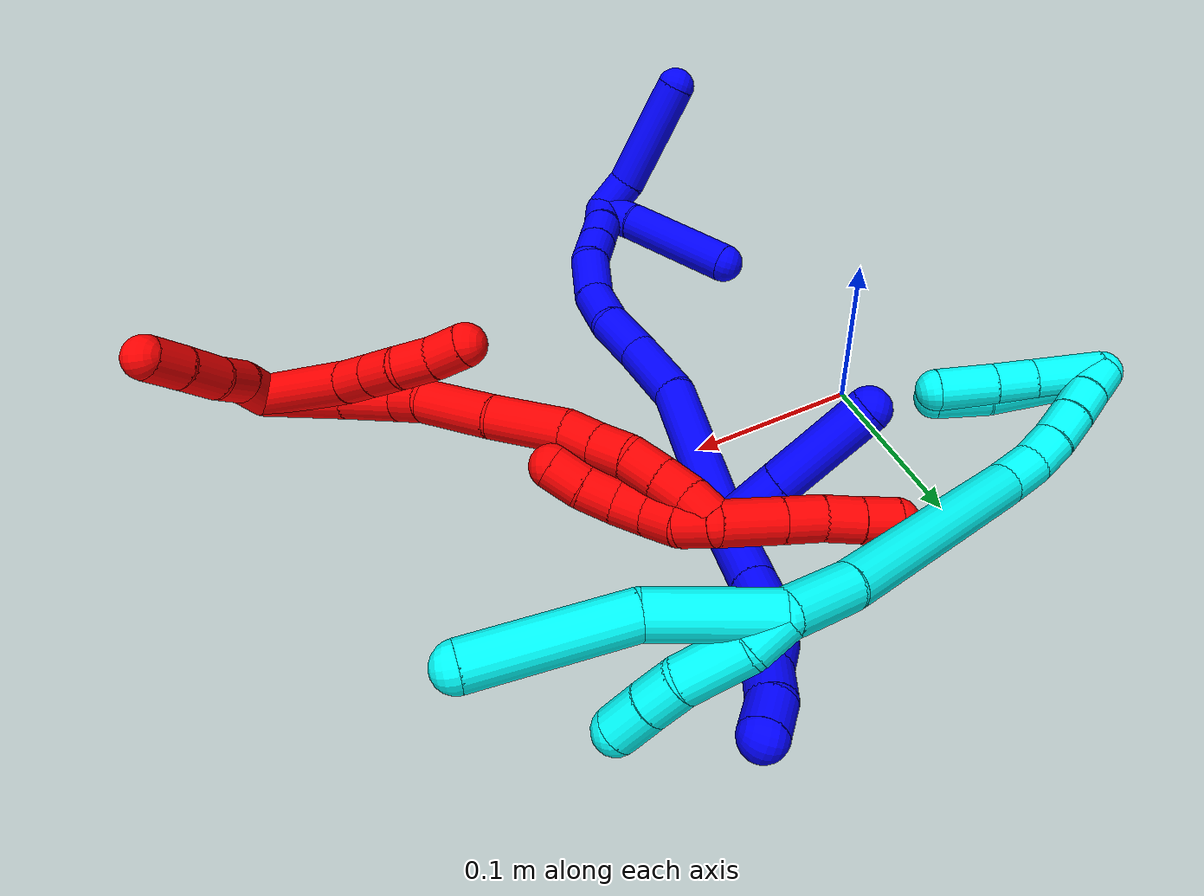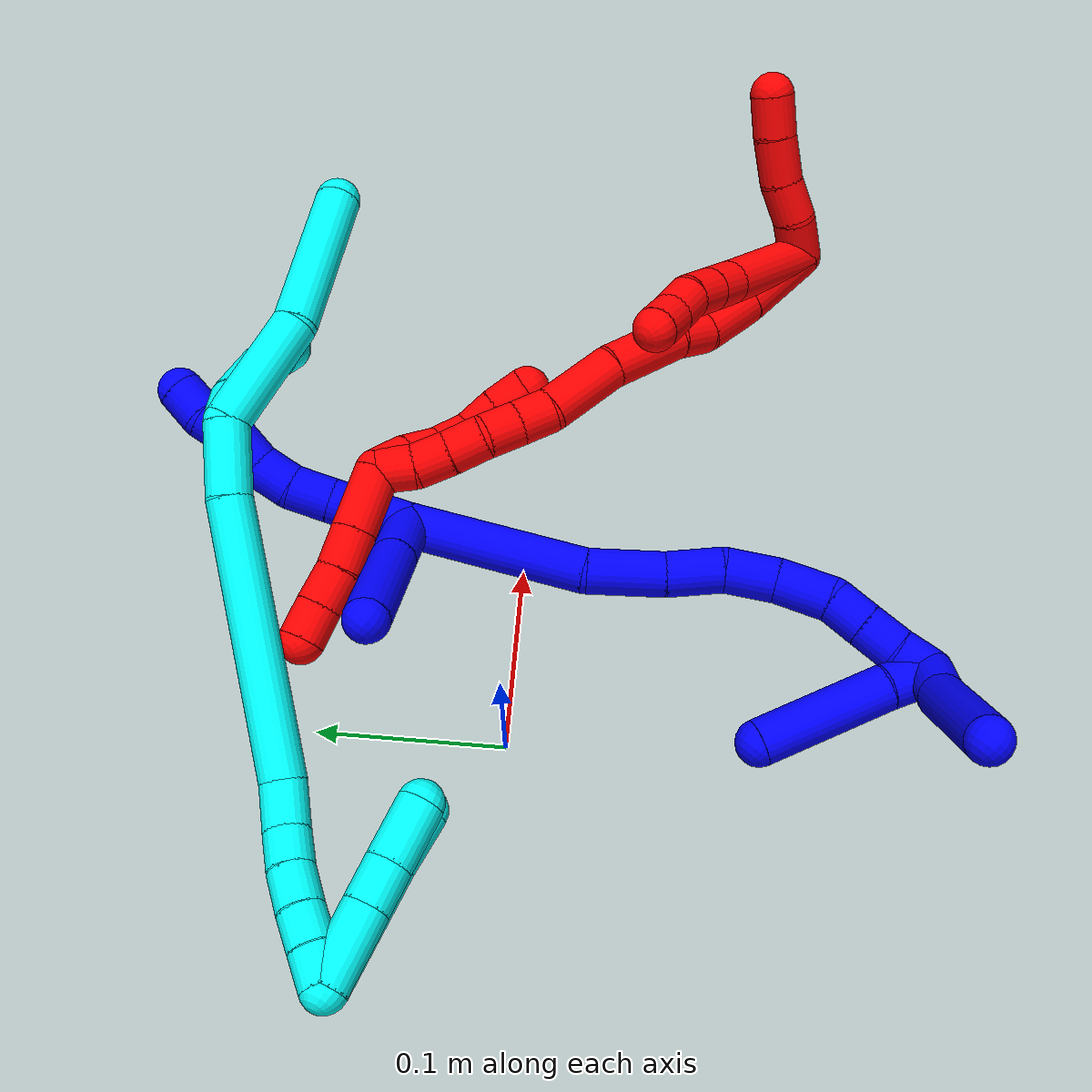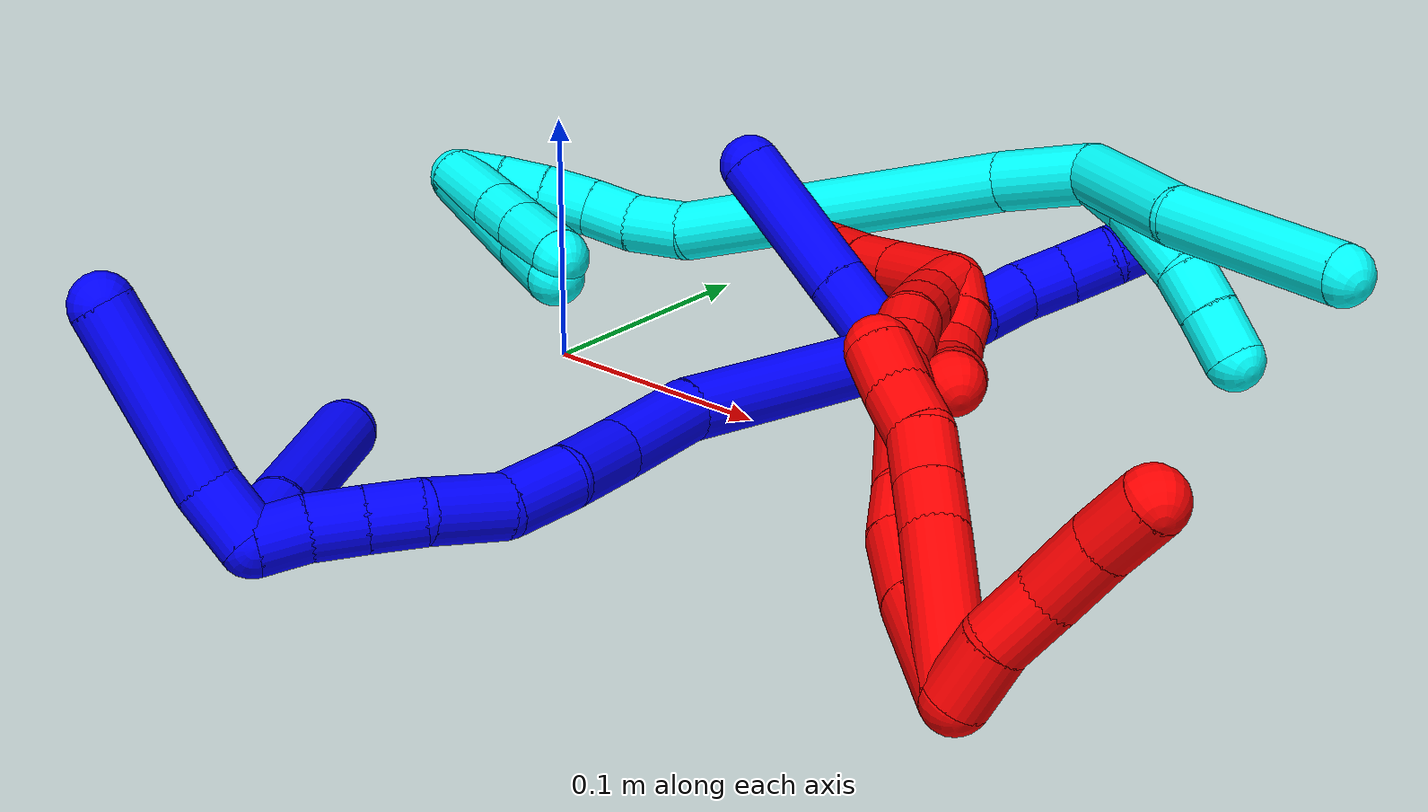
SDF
<sdf version="1.7">
 <world name="default">
  <plugin name="TubeGeneratorPlugin" filename="libtube_generator_plugin.so"/>
  <model name="photoneo_s_sensor">
   <static>1</static>
   <pose>0 0 2 1.57079 1.57079 3.14159</pose>
   <link name="link">
    <inertial><mass>0.1</mass></inertial>
    <sensor name="sensor" type="depth">
     <update_rate>30</update_rate>
     <camera>
      <horizontal_fov>1.22</horizontal_fov>
      <image><width>1920</width><height>1200</height><format>B8G8R8</format></image>
      <clip><near>0.1</near><far>4</far></clip>
      <depth_camera><output>points</output></depth_camera>
     </camera>
     <plugin name="camera_plugin" filename="libgazebo_ros_depth_camera.so">
      <baseline>0.2</baseline>
      <alwaysOn>1</alwaysOn>
      <updateRate>0.0</updateRate>
      <cameraName>camera_ir</cameraName>
      <imageTopicName>/camera/color/image_raw</imageTopicName>
      <cameraInfoTopicName>/camera/color/camera_info</cameraInfoTopicName>
      <depthImageTopicName>/camera/depth/image_raw</depthImageTopicName>
      <depthImageCameraInfoTopicName>/camera/depth/camera_info</depthImageCameraInfoTopicName>
      <pointCloudTopicName>/camera/depth/points</pointCloudTopicName>
      <frameName>fr_optical</frameName>
      <pointCloudCutoff>0.1</pointCloudCutoff>
      <pointCloudCutoffMax>2.0</pointCloudCutoffMax>
      <distortionK1>0</distortionK1>
      <distortionK2>0</distortionK2>
      <distortionK3>0</distortionK3>
      <distortionT1>0</distortionT1>
      <distortionT2>0</distortionT2>
      <CxPrime>0</CxPrime>
      <Cx>0</Cx>
      <Cy>0</Cy>
      <focalLength>0</focalLength>
      <hackBaseline>0</hackBaseline>
     </plugin>
    </sensor>
   </link>
  </model>
  <gravity>0 0 -9.8</gravity>
  <magnetic_field>6e-06 2.3e-05 -4.2e-05</magnetic_field>
  <atmosphere type="adiabatic"/>
  <physics name="default_physics" default="0" type="ode">
   <max_step_size>0.003</max_step_size>
   <real_time_factor>1</real_time_factor>
   <real_time_update_rate>1000</real_time_update_rate>
   <max_contacts>10000</max_contacts>
   <ode>
    <solver>
     <type>quick</type>
     <iters>100</iters>
     <sor>1.3</sor>
     <use_dynamic_moi_rescaling>0</use_dynamic_moi_rescaling>
    </solver>
    <constraints>
     <contact_max_correcting_vel>0</contact_max_correcting_vel>
     <contact_surface_layer>0.001</contact_surface_layer>
     <cfm>0</cfm>
     <erp>0.2</erp>
    </constraints>
   </ode>
  </physics>
  <scene><ambient>0.4 0.4 0.4 1</ambient><background>0.7 0.7 0.7 1</background><shadows>0</shadows></scene>
  <audio><device>default</device></audio>
  <spherical_coordinates>
   <surface_model>EARTH_WGS84</surface_model>
   <latitude_deg>0</latitude_deg>
   <longitude_deg>0</longitude_deg>
   <elevation>0</elevation>
   <heading_deg>0</heading_deg>
  </spherical_coordinates>
  <model name="bin">
   <static>1</static>
   <link name="bottom">
    <collision name="collision-bottom">
     <pose>0 0 -0.01 0 -0 0</pose>
     <geometry><box><size>0.8 0.6 0.02</size></box></geometry>
     <surface>
      <friction><ode><mu>100</mu><mu2>100</mu2></ode></friction>
      <contact><collide_bitmask>65535</collide_bitmask></contact>
     </surface>
    </collision>
   </link>
   <link name="west_wall">
    <collision name="collision-west_wall">
     <pose>-0.41 0 0.1 0 -0 0</pose>
     <geometry><box><size>0.02 0.6 0.2</size></box></geometry>
     <surface>
      <friction><ode><mu>100</mu><mu2>100</mu2></ode></friction>
      <contact><collide_bitmask>65535</collide_bitmask></contact>
     </surface>
    </collision>
   </link>
   <link name="east_wall">
    <collision name="collision-east_wall">
     <pose>0.41 0 0.1 0 -0 0</pose>
     <geometry><box><size>0.02 0.6 0.2</size></box></geometry>
     <surface>
      <friction><ode><mu>100</mu><mu2>100</mu2></ode></friction>
      <contact><collide_bitmask>65535</collide_bitmask></contact>
     </surface>
    </collision>
   </link>
   <link name="south_wall">
    <collision name="collision-south_wall">
     <pose>0 -0.31 0.1 0 -0 0</pose>
     <geometry><box><size>0.8 0.02 0.2</size></box></geometry>
     <surface>
      <friction><ode><mu>100</mu><mu2>100</mu2></ode></friction>
      <contact><collide_bitmask>65535</collide_bitmask></contact>
     </surface>
    </collision>
   </link>
   <link name="north_wall">
    <collision name="collision-north_wall">
     <pose>0 0.31 0.1 0 -0 0</pose>
     <geometry><box><size>0.8 0.02 0.2</size></box></geometry>
     <surface>
      <friction><ode><mu>100</mu><mu2>100</mu2></ode></friction>
      <contact><collide_bitmask>65535</collide_bitmask></contact>
     </surface>
    </collision>
   </link>
  </model>
  <model name="1">
   <static>0</static>
   <link name="1">
    <collision name="collision-cylinder-e_1_2_8">
     <pose>0.009217 0.018698 -0.007852 -1.96836 0.426588 -0.630017</pose>
     <geometry><cylinder><radius>0.0125</radius><length>0.044551</length></cylinder></geometry>
     <surface>
      <friction><ode><mu>1.16</mu><mu2>1.16</mu2><slip1>0</slip1><slip2>0</slip2></ode></friction>
      <contact><ode><kp>1e+06</kp><kd>1</kd><max_vel>0</max_vel><min_depth>0.001</min_depth></ode></contact>
     </surface>
    </collision>
    <visual name="visual-cylinder-e_1_2_8">
     <pose>0.009217 0.018698 -0.007852 -1.96836 0.426588 -0.630017</pose>
     <geometry><cylinder><radius>0.0125</radius><length>0.044551</length></cylinder></geometry>
     <material><ambient>0 0 1 1</ambient></material>
    </visual>
    <collision name="collision-cylinder-e_2_8_9">
     <pose>0.022917 0.04722 -0.019466 -1.93661 0.402865 -0.577205</pose>
     <geometry><cylinder><radius>0.0125</radius><length>0.022872</length></cylinder></geometry>
     <surface>
      <friction><ode><mu>1.16</mu><mu2>1.16</mu2><slip1>0</slip1><slip2>0</slip2></ode></friction>
      <contact><ode><kp>1e+06</kp><kd>1</kd><max_vel>0</max_vel><min_depth>0.001</min_depth></ode></contact>
     </surface>
    </collision>
    <visual name="visual-cylinder-e_2_8_9">
     <pose>0.022917 0.04722 -0.019466 -1.93661 0.402865 -0.577205</pose>
     <geometry><cylinder><radius>0.0125</radius><length>0.022872</length></cylinder></geometry>
     <material><ambient>0 0 1 1</ambient></material>
    </visual>
    <collision name="collision-cylinder-e_3_9_10">
     <pose>0.03228 0.066507 -0.024165 -1.66935 0.474078 -0.521163</pose>
     <geometry><cylinder><radius>0.0125</radius><length>0.021375</length></cylinder></geometry>
     <surface>
      <friction><ode><mu>1.16</mu><mu2>1.16</mu2><slip1>0</slip1><slip2>0</slip2></ode></friction>
      <contact><ode><kp>1e+06</kp><kd>1</kd><max_vel>0</max_vel><min_depth>0.001</min_depth></ode></contact>
     </surface>
    </collision>
    <visual name="visual-cylinder-e_3_9_10">
     <pose>0.03228 0.066507 -0.024165 -1.66935 0.474078 -0.521163</pose>
     <geometry><cylinder><radius>0.0125</radius><length>0.021375</length></cylinder></geometry>
     <material><ambient>0 0 1 1</ambient></material>
    </visual>
    <collision name="collision-cylinder-e_4_10_11">
     <pose>0.041118 0.085342 -0.023075 -1.35791 0.391568 -0.317378</pose>
     <geometry><cylinder><radius>0.0125</radius><length>0.020748</length></cylinder></geometry>
     <surface>
      <friction><ode><mu>1.16</mu><mu2>1.16</mu2><slip1>0</slip1><slip2>0</slip2></ode></friction>
      <contact><ode><kp>1e+06</kp><kd>1</kd><max_vel>0</max_vel><min_depth>0.001</min_depth></ode></contact>
     </surface>
    </collision>
    <visual name="visual-cylinder-e_4_10_11">
     <pose>0.041118 0.085342 -0.023075 -1.35791 0.391568 -0.317378</pose>
     <geometry><cylinder><radius>0.0125</radius><length>0.020748</length></cylinder></geometry>
     <material><ambient>0 0 1 1</ambient></material>
    </visual>
    <collision name="collision-cylinder-e_5_11_12">
     <pose>0.049464 0.103853 -0.021853 -1.65856 0.446046 -0.485487</pose>
     <geometry><cylinder><radius>0.0125</radius><length>0.020338</length></cylinder></geometry>
     <surface>
      <friction><ode><mu>1.16</mu><mu2>1.16</mu2><slip1>0</slip1><slip2>0</slip2></ode></friction>
      <contact><ode><kp>1e+06</kp><kd>1</kd><max_vel>0</max_vel><min_depth>0.001</min_depth></ode></contact>
     </surface>
    </collision>
    <visual name="visual-cylinder-e_5_11_12">
     <pose>0.049464 0.103853 -0.021853 -1.65856 0.446046 -0.485487</pose>
     <geometry><cylinder><radius>0.0125</radius><length>0.020338</length></cylinder></geometry>
     <material><ambient>0 0 1 1</ambient></material>
    </visual>
    <collision name="collision-cylinder-e_6_12_6">
     <pose>0.059455 0.121148 -0.02086 -1.35389 0.591011 -0.479847</pose>
     <geometry><cylinder><radius>0.0125</radius><length>0.020115</length></cylinder></geometry>
     <surface>
      <friction><ode><mu>1.16</mu><mu2>1.16</mu2><slip1>0</slip1><slip2>0</slip2></ode></friction>
      <contact><ode><kp>1e+06</kp><kd>1</kd><max_vel>0</max_vel><min_depth>0.001</min_depth></ode></contact>
     </surface>
    </collision>
    <visual name="visual-cylinder-e_6_12_6">
     <pose>0.059455 0.121148 -0.02086 -1.35389 0.591011 -0.479847</pose>
     <geometry><cylinder><radius>0.0125</radius><length>0.020115</length></cylinder></geometry>
     <material><ambient>0 0 1 1</ambient></material>
    </visual>
    <collision name="collision-cylinder-e_1_2_13">
     <pose>-0.016197 0.003855 -0.009534 -2.75739 -1.00508 2.46133</pose>
     <geometry><cylinder><radius>0.0125</radius><length>0.038371</length></cylinder></geometry>
     <surface>
      <friction><ode><mu>1.16</mu><mu2>1.16</mu2><slip1>0</slip1><slip2>0</slip2></ode></friction>
      <contact><ode><kp>1e+06</kp><kd>1</kd><max_vel>0</max_vel><min_depth>0.001</min_depth></ode></contact>
     </surface>
    </collision>
    <visual name="visual-cylinder-e_1_2_13">
     <pose>-0.016197 0.003855 -0.009534 -2.75739 -1.00508 2.46133</pose>
     <geometry><cylinder><radius>0.0125</radius><length>0.038371</length></cylinder></geometry>
     <material><ambient>0 0 1 1</ambient></material>
    </visual>
    <collision name="collision-cylinder-e_2_13_5">
     <pose>-0.058392 0.013996 -0.034368 -2.7517 -1.00415 2.45108</pose>
     <geometry><cylinder><radius>0.0125</radius><length>0.061629</length></cylinder></geometry>
     <surface>
      <friction><ode><mu>1.16</mu><mu2>1.16</mu2><slip1>0</slip1><slip2>0</slip2></ode></friction>
      <contact><ode><kp>1e+06</kp><kd>1</kd><max_vel>0</max_vel><min_depth>0.001</min_depth></ode></contact>
     </surface>
    </collision>
    <visual name="visual-cylinder-e_2_13_5">
     <pose>-0.058392 0.013996 -0.034368 -2.7517 -1.00415 2.45108</pose>
     <geometry><cylinder><radius>0.0125</radius><length>0.061629</length></cylinder></geometry>
     <material><ambient>0 0 1 1</ambient></material>
    </visual>
    <collision name="collision-cylinder-e_1_2_14">
     <pose>-0.02821 -0.037381 0.019695 1.08587 -0.588679 -0.361852</pose>
     <geometry><cylinder><radius>0.0125</radius><length>0.101608</length></cylinder></geometry>
     <surface>
      <friction><ode><mu>1.16</mu><mu2>1.16</mu2><slip1>0</slip1><slip2>0</slip2></ode></friction>
      <contact><ode><kp>1e+06</kp><kd>1</kd><max_vel>0</max_vel><min_depth>0.001</min_depth></ode></contact>
     </surface>
    </collision>
    <visual name="visual-cylinder-e_1_2_14">
     <pose>-0.02821 -0.037381 0.019695 1.08587 -0.588679 -0.361852</pose>
     <geometry><cylinder><radius>0.0125</radius><length>0.101608</length></cylinder></geometry>
     <material><ambient>0 0 1 1</ambient></material>
    </visual>
    <collision name="collision-cylinder-e_2_14_15">
     <pose>-0.064313 -0.09049 0.051932 0.897652 -0.373949 -0.181723</pose>
     <geometry><cylinder><radius>0.0125</radius><length>0.043218</length></cylinder></geometry>
     <surface>
      <friction><ode><mu>1.16</mu><mu2>1.16</mu2><slip1>0</slip1><slip2>0</slip2></ode></friction>
      <contact><ode><kp>1e+06</kp><kd>1</kd><max_vel>0</max_vel><min_depth>0.001</min_depth></ode></contact>
     </surface>
    </collision>
    <visual name="visual-cylinder-e_2_14_15">
     <pose>-0.064313 -0.09049 0.051932 0.897652 -0.373949 -0.181723</pose>
     <geometry><cylinder><radius>0.0125</radius><length>0.043218</length></cylinder></geometry>
     <material><ambient>0 0 1 1</ambient></material>
    </visual>
    <collision name="collision-cylinder-e_3_15_16">
     <pose>-0.0781 -0.11625 0.075147 0.754414 -0.382493 -0.15311</pose>
     <geometry><cylinder><radius>0.0125</radius><length>0.031578</length></cylinder></geometry>
     <surface>
      <friction><ode><mu>1.16</mu><mu2>1.16</mu2><slip1>0</slip1><slip2>0</slip2></ode></friction>
      <contact><ode><kp>1e+06</kp><kd>1</kd><max_vel>0</max_vel><min_depth>0.001</min_depth></ode></contact>
     </surface>
    </collision>
    <visual name="visual-cylinder-e_3_15_16">
     <pose>-0.0781 -0.11625 0.075147 0.754414 -0.382493 -0.15311</pose>
     <geometry><cylinder><radius>0.0125</radius><length>0.031578</length></cylinder></geometry>
     <material><ambient>0 0 1 1</ambient></material>
    </visual>
    <collision name="collision-cylinder-e_4_16_17">
     <pose>-0.090243 -0.137858 0.09246 1.0501 -0.438046 -0.256476</pose>
     <geometry><cylinder><radius>0.0125</radius><length>0.029473</length></cylinder></geometry>
     <surface>
      <friction><ode><mu>1.16</mu><mu2>1.16</mu2><slip1>0</slip1><slip2>0</slip2></ode></friction>
      <contact><ode><kp>1e+06</kp><kd>1</kd><max_vel>0</max_vel><min_depth>0.001</min_depth></ode></contact>
     </surface>
    </collision>
    <visual name="visual-cylinder-e_4_16_17">
     <pose>-0.090243 -0.137858 0.09246 1.0501 -0.438046 -0.256476</pose>
     <geometry><cylinder><radius>0.0125</radius><length>0.029473</length></cylinder></geometry>
     <material><ambient>0 0 1 1</ambient></material>
    </visual>
    <collision name="collision-cylinder-e_5_17_18">
     <pose>-0.10752 -0.159902 0.103599 1.16473 -0.768977 -0.520833</pose>
     <geometry><cylinder><radius>0.0125</radius><length>0.031711</length></cylinder></geometry>
     <surface>
      <friction><ode><mu>1.16</mu><mu2>1.16</mu2><slip1>0</slip1><slip2>0</slip2></ode></friction>
      <contact><ode><kp>1e+06</kp><kd>1</kd><max_vel>0</max_vel><min_depth>0.001</min_depth></ode></contact>
     </surface>
    </collision>
    <visual name="visual-cylinder-e_5_17_18">
     <pose>-0.10752 -0.159902 0.103599 1.16473 -0.768977 -0.520833</pose>
     <geometry><cylinder><radius>0.0125</radius><length>0.031711</length></cylinder></geometry>
     <material><ambient>0 0 1 1</ambient></material>
    </visual>
    <collision name="collision-cylinder-e_6_18_19">
     <pose>-0.12534 -0.17846 0.107661 1.62495 -0.69783 -0.733373</pose>
     <geometry><cylinder><radius>0.0125</radius><length>0.021148</length></cylinder></geometry>
     <surface>
      <friction><ode><mu>1.16</mu><mu2>1.16</mu2><slip1>0</slip1><slip2>0</slip2></ode></friction>
      <contact><ode><kp>1e+06</kp><kd>1</kd><max_vel>0</max_vel><min_depth>0.001</min_depth></ode></contact>
     </surface>
    </collision>
    <visual name="visual-cylinder-e_6_18_19">
     <pose>-0.12534 -0.17846 0.107661 1.62495 -0.69783 -0.733373</pose>
     <geometry><cylinder><radius>0.0125</radius><length>0.021148</length></cylinder></geometry>
     <material><ambient>0 0 1 1</ambient></material>
    </visual>
    <collision name="collision-cylinder-e_7_19_20">
     <pose>-0.138791 -0.19472 0.106925 1.60721 -0.683359 -0.70668</pose>
     <geometry><cylinder><radius>0.0125</radius><length>0.021085</length></cylinder></geometry>
     <surface>
      <friction><ode><mu>1.16</mu><mu2>1.16</mu2><slip1>0</slip1><slip2>0</slip2></ode></friction>
      <contact><ode><kp>1e+06</kp><kd>1</kd><max_vel>0</max_vel><min_depth>0.001</min_depth></ode></contact>
     </surface>
    </collision>
    <visual name="visual-cylinder-e_7_19_20">
     <pose>-0.138791 -0.19472 0.106925 1.60721 -0.683359 -0.70668</pose>
     <geometry><cylinder><radius>0.0125</radius><length>0.021085</length></cylinder></geometry>
     <material><ambient>0 0 1 1</ambient></material>
    </visual>
    <collision name="collision-cylinder-e_8_20_1">
     <pose>-0.150844 -0.21138 0.107406 1.47936 -0.564308 -0.517202</pose>
     <geometry><cylinder><radius>0.0125</radius><length>0.020179</length></cylinder></geometry>
     <surface>
      <friction><ode><mu>1.16</mu><mu2>1.16</mu2><slip1>0</slip1><slip2>0</slip2></ode></friction>
      <contact><ode><kp>1e+06</kp><kd>1</kd><max_vel>0</max_vel><min_depth>0.001</min_depth></ode></contact>
     </surface>
    </collision>
    <visual name="visual-cylinder-e_8_20_1">
     <pose>-0.150844 -0.21138 0.107406 1.47936 -0.564308 -0.517202</pose>
     <geometry><cylinder><radius>0.0125</radius><length>0.020179</length></cylinder></geometry>
     <material><ambient>0 0 1 1</ambient></material>
    </visual>
    <collision name="collision-cylinder-e_1_1_21">
     <pose>-0.168106 -0.217946 0.103552 -2.74802 -1.17093 2.55739</pose>
     <geometry><cylinder><radius>0.0125</radius><length>0.025765</length></cylinder></geometry>
     <surface>
      <friction><ode><mu>1.16</mu><mu2>1.16</mu2><slip1>0</slip1><slip2>0</slip2></ode></friction>
      <contact><ode><kp>1e+06</kp><kd>1</kd><max_vel>0</max_vel><min_depth>0.001</min_depth></ode></contact>
     </surface>
    </collision>
    <visual name="visual-cylinder-e_1_1_21">
     <pose>-0.168106 -0.217946 0.103552 -2.74802 -1.17093 2.55739</pose>
     <geometry><cylinder><radius>0.0125</radius><length>0.025765</length></cylinder></geometry>
     <material><ambient>0 0 1 1</ambient></material>
    </visual>
    <collision name="collision-cylinder-e_2_21_4">
     <pose>-0.215001 -0.205161 0.093201 -2.05552 -1.23373 1.73136</pose>
     <geometry><cylinder><radius>0.0125</radius><length>0.074235</length></cylinder></geometry>
     <surface>
      <friction><ode><mu>1.16</mu><mu2>1.16</mu2><slip1>0</slip1><slip2>0</slip2></ode></friction>
      <contact><ode><kp>1e+06</kp><kd>1</kd><max_vel>0</max_vel><min_depth>0.001</min_depth></ode></contact>
     </surface>
    </collision>
    <visual name="visual-cylinder-e_2_21_4">
     <pose>-0.215001 -0.205161 0.093201 -2.05552 -1.23373 1.73136</pose>
     <geometry><cylinder><radius>0.0125</radius><length>0.074235</length></cylinder></geometry>
     <material><ambient>0 0 1 1</ambient></material>
    </visual>
    <collision name="collision-cylinder-e_1_1_22">
     <pose>-0.155247 -0.212414 0.097483 -2.53308 0.075986 -0.240935</pose>
     <geometry><cylinder><radius>0.0125</radius><length>0.02616</length></cylinder></geometry>
     <surface>
      <friction><ode><mu>1.16</mu><mu2>1.16</mu2><slip1>0</slip1><slip2>0</slip2></ode></friction>
      <contact><ode><kp>1e+06</kp><kd>1</kd><max_vel>0</max_vel><min_depth>0.001</min_depth></ode></contact>
     </surface>
    </collision>
    <visual name="visual-cylinder-e_1_1_22">
     <pose>-0.155247 -0.212414 0.097483 -2.53308 0.075986 -0.240935</pose>
     <geometry><cylinder><radius>0.0125</radius><length>0.02616</length></cylinder></geometry>
     <material><ambient>0 0 1 1</ambient></material>
    </visual>
    <collision name="collision-cylinder-e_2_22_3">
     <pose>-0.149311 -0.18718 0.054804 -2.63418 0.134294 -0.507525</pose>
     <geometry><cylinder><radius>0.0125</radius><length>0.07384</length></cylinder></geometry>
     <surface>
      <friction><ode><mu>1.16</mu><mu2>1.16</mu2><slip1>0</slip1><slip2>0</slip2></ode></friction>
      <contact><ode><kp>1e+06</kp><kd>1</kd><max_vel>0</max_vel><min_depth>0.001</min_depth></ode></contact>
     </surface>
    </collision>
    <visual name="visual-cylinder-e_2_22_3">
     <pose>-0.149311 -0.18718 0.054804 -2.63418 0.134294 -0.507525</pose>
     <geometry><cylinder><radius>0.0125</radius><length>0.07384</length></cylinder></geometry>
     <material><ambient>0 0 1 1</ambient></material>
    </visual>
    <collision name="collision-sphere-3">
     <pose>-0.144368 -0.169401 0.022826 0 -0 0</pose>
     <geometry><sphere><radius>0.0125</radius></sphere></geometry>
     <surface>
      <friction><ode><mu>1.16</mu><mu2>1.16</mu2><slip1>0</slip1><slip2>0</slip2></ode></friction>
      <contact><ode><kp>1e+06</kp><kd>1</kd><max_vel>0</max_vel><min_depth>0.001</min_depth></ode></contact>
     </surface>
    </collision>
    <visual name="visual-sphere-3">
     <pose>-0.144368 -0.169401 0.022826 0 -0 0</pose>
     <geometry><sphere><radius>0.0125</radius></sphere></geometry>
     <material><ambient>0 0 1 1</ambient></material>
    </visual>
    <collision name="collision-sphere-22">
     <pose>-0.154254 -0.204958 0.086781 0 -0 0</pose>
     <geometry><sphere><radius>0.0125</radius></sphere></geometry>
     <surface>
      <friction><ode><mu>1.16</mu><mu2>1.16</mu2><slip1>0</slip1><slip2>0</slip2></ode></friction>
      <contact><ode><kp>1e+06</kp><kd>1</kd><max_vel>0</max_vel><min_depth>0.001</min_depth></ode></contact>
     </surface>
    </collision>
    <visual name="visual-sphere-22">
     <pose>-0.154254 -0.204958 0.086781 0 -0 0</pose>
     <geometry><sphere><radius>0.0125</radius></sphere></geometry>
     <material><ambient>0 0 1 1</ambient></material>
    </visual>
    <collision name="collision-sphere-4">
     <pose>-0.25003 -0.1943 0.087481 0 -0 0</pose>
     <geometry><sphere><radius>0.0125</radius></sphere></geometry>
     <surface>
      <friction><ode><mu>1.16</mu><mu2>1.16</mu2><slip1>0</slip1><slip2>0</slip2></ode></friction>
      <contact><ode><kp>1e+06</kp><kd>1</kd><max_vel>0</max_vel><min_depth>0.001</min_depth></ode></contact>
     </surface>
    </collision>
    <visual name="visual-sphere-4">
     <pose>-0.25003 -0.1943 0.087481 0 -0 0</pose>
     <geometry><sphere><radius>0.0125</radius></sphere></geometry>
     <material><ambient>0 0 1 1</ambient></material>
    </visual>
    <collision name="collision-sphere-21">
     <pose>-0.179973 -0.216023 0.098921 0 -0 0</pose>
     <geometry><sphere><radius>0.0125</radius></sphere></geometry>
     <surface>
      <friction><ode><mu>1.16</mu><mu2>1.16</mu2><slip1>0</slip1><slip2>0</slip2></ode></friction>
      <contact><ode><kp>1e+06</kp><kd>1</kd><max_vel>0</max_vel><min_depth>0.001</min_depth></ode></contact>
     </surface>
    </collision>
    <visual name="visual-sphere-21">
     <pose>-0.179973 -0.216023 0.098921 0 -0 0</pose>
     <geometry><sphere><radius>0.0125</radius></sphere></geometry>
     <material><ambient>0 0 1 1</ambient></material>
    </visual>
    <collision name="collision-sphere-1">
     <pose>-0.15624 -0.219869 0.108184 0 -0 0</pose>
     <geometry><sphere><radius>0.0125</radius></sphere></geometry>
     <surface>
      <friction><ode><mu>1.16</mu><mu2>1.16</mu2><slip1>0</slip1><slip2>0</slip2></ode></friction>
      <contact><ode><kp>1e+06</kp><kd>1</kd><max_vel>0</max_vel><min_depth>0.001</min_depth></ode></contact>
     </surface>
    </collision>
    <visual name="visual-sphere-1">
     <pose>-0.15624 -0.219869 0.108184 0 -0 0</pose>
     <geometry><sphere><radius>0.0125</radius></sphere></geometry>
     <material><ambient>0 0 1 1</ambient></material>
    </visual>
    <collision name="collision-sphere-12">
     <pose>0.053851 0.112992 -0.022657 0 -0 0</pose>
     <geometry><sphere><radius>0.0125</radius></sphere></geometry>
     <surface>
      <friction><ode><mu>1.16</mu><mu2>1.16</mu2><slip1>0</slip1><slip2>0</slip2></ode></friction>
      <contact><ode><kp>1e+06</kp><kd>1</kd><max_vel>0</max_vel><min_depth>0.001</min_depth></ode></contact>
     </surface>
    </collision>
    <visual name="visual-sphere-12">
     <pose>0.053851 0.112992 -0.022657 0 -0 0</pose>
     <geometry><sphere><radius>0.0125</radius></sphere></geometry>
     <material><ambient>0 0 1 1</ambient></material>
    </visual>
    <collision name="collision-sphere-11">
     <pose>0.045077 0.094715 -0.021049 0 -0 0</pose>
     <geometry><sphere><radius>0.0125</radius></sphere></geometry>
     <surface>
      <friction><ode><mu>1.16</mu><mu2>1.16</mu2><slip1>0</slip1><slip2>0</slip2></ode></friction>
      <contact><ode><kp>1e+06</kp><kd>1</kd><max_vel>0</max_vel><min_depth>0.001</min_depth></ode></contact>
     </surface>
    </collision>
    <visual name="visual-sphere-11">
     <pose>0.045077 0.094715 -0.021049 0 -0 0</pose>
     <geometry><sphere><radius>0.0125</radius></sphere></geometry>
     <material><ambient>0 0 1 1</ambient></material>
    </visual>
    <collision name="collision-sphere-10">
     <pose>0.037159 0.07597 -0.025101 0 -0 0</pose>
     <geometry><sphere><radius>0.0125</radius></sphere></geometry>
     <surface>
      <friction><ode><mu>1.16</mu><mu2>1.16</mu2><slip1>0</slip1><slip2>0</slip2></ode></friction>
      <contact><ode><kp>1e+06</kp><kd>1</kd><max_vel>0</max_vel><min_depth>0.001</min_depth></ode></contact>
     </surface>
    </collision>
    <visual name="visual-sphere-10">
     <pose>0.037159 0.07597 -0.025101 0 -0 0</pose>
     <geometry><sphere><radius>0.0125</radius></sphere></geometry>
     <material><ambient>0 0 1 1</ambient></material>
    </visual>
    <collision name="collision-sphere-9">
     <pose>0.027401 0.057045 -0.02323 0 -0 0</pose>
     <geometry><sphere><radius>0.0125</radius></sphere></geometry>
     <surface>
      <friction><ode><mu>1.16</mu><mu2>1.16</mu2><slip1>0</slip1><slip2>0</slip2></ode></friction>
      <contact><ode><kp>1e+06</kp><kd>1</kd><max_vel>0</max_vel><min_depth>0.001</min_depth></ode></contact>
     </surface>
    </collision>
    <visual name="visual-sphere-9">
     <pose>0.027401 0.057045 -0.02323 0 -0 0</pose>
     <geometry><sphere><radius>0.0125</radius></sphere></geometry>
     <material><ambient>0 0 1 1</ambient></material>
    </visual>
    <collision name="collision-sphere-2">
     <geometry><sphere><radius>0.0125</radius></sphere></geometry>
     <surface>
      <friction><ode><mu>1.16</mu><mu2>1.16</mu2><slip1>0</slip1><slip2>0</slip2></ode></friction>
      <contact><ode><kp>1e+06</kp><kd>1</kd><max_vel>0</max_vel><min_depth>0.001</min_depth></ode></contact>
     </surface>
    </collision>
    <visual name="visual-sphere-2">
     <geometry><sphere><radius>0.0125</radius></sphere></geometry>
     <material><ambient>0 0 1 1</ambient></material>
    </visual>
    <collision name="collision-sphere-19">
     <pose>-0.132134 -0.18655 0.107223 0 -0 0</pose>
     <geometry><sphere><radius>0.0125</radius></sphere></geometry>
     <surface>
      <friction><ode><mu>1.16</mu><mu2>1.16</mu2><slip1>0</slip1><slip2>0</slip2></ode></friction>
      <contact><ode><kp>1e+06</kp><kd>1</kd><max_vel>0</max_vel><min_depth>0.001</min_depth></ode></contact>
     </surface>
    </collision>
    <visual name="visual-sphere-19">
     <pose>-0.132134 -0.18655 0.107223 0 -0 0</pose>
     <geometry><sphere><radius>0.0125</radius></sphere></geometry>
     <material><ambient>0 0 1 1</ambient></material>
    </visual>
    <collision name="collision-sphere-8">
     <pose>0.018434 0.037396 -0.015703 0 -0 0</pose>
     <geometry><sphere><radius>0.0125</radius></sphere></geometry>
     <surface>
      <friction><ode><mu>1.16</mu><mu2>1.16</mu2><slip1>0</slip1><slip2>0</slip2></ode></friction>
      <contact><ode><kp>1e+06</kp><kd>1</kd><max_vel>0</max_vel><min_depth>0.001</min_depth></ode></contact>
     </surface>
    </collision>
    <visual name="visual-sphere-8">
     <pose>0.018434 0.037396 -0.015703 0 -0 0</pose>
     <geometry><sphere><radius>0.0125</radius></sphere></geometry>
     <material><ambient>0 0 1 1</ambient></material>
    </visual>
    <collision name="collision-sphere-6">
     <pose>0.065059 0.129304 -0.019062 0 -0 0</pose>
     <geometry><sphere><radius>0.0125</radius></sphere></geometry>
     <surface>
      <friction><ode><mu>1.16</mu><mu2>1.16</mu2><slip1>0</slip1><slip2>0</slip2></ode></friction>
      <contact><ode><kp>1e+06</kp><kd>1</kd><max_vel>0</max_vel><min_depth>0.001</min_depth></ode></contact>
     </surface>
    </collision>
    <visual name="visual-sphere-6">
     <pose>0.065059 0.129304 -0.019062 0 -0 0</pose>
     <geometry><sphere><radius>0.0125</radius></sphere></geometry>
     <material><ambient>0 0 1 1</ambient></material>
    </visual>
    <collision name="collision-sphere-13">
     <pose>-0.032393 0.007709 -0.019068 0 -0 0</pose>
     <geometry><sphere><radius>0.0125</radius></sphere></geometry>
     <surface>
      <friction><ode><mu>1.16</mu><mu2>1.16</mu2><slip1>0</slip1><slip2>0</slip2></ode></friction>
      <contact><ode><kp>1e+06</kp><kd>1</kd><max_vel>0</max_vel><min_depth>0.001</min_depth></ode></contact>
     </surface>
    </collision>
    <visual name="visual-sphere-13">
     <pose>-0.032393 0.007709 -0.019068 0 -0 0</pose>
     <geometry><sphere><radius>0.0125</radius></sphere></geometry>
     <material><ambient>0 0 1 1</ambient></material>
    </visual>
    <collision name="collision-sphere-5">
     <pose>-0.08439 0.020283 -0.049668 0 -0 0</pose>
     <geometry><sphere><radius>0.0125</radius></sphere></geometry>
     <surface>
      <friction><ode><mu>1.16</mu><mu2>1.16</mu2><slip1>0</slip1><slip2>0</slip2></ode></friction>
      <contact><ode><kp>1e+06</kp><kd>1</kd><max_vel>0</max_vel><min_depth>0.001</min_depth></ode></contact>
     </surface>
    </collision>
    <visual name="visual-sphere-5">
     <pose>-0.08439 0.020283 -0.049668 0 -0 0</pose>
     <geometry><sphere><radius>0.0125</radius></sphere></geometry>
     <material><ambient>0 0 1 1</ambient></material>
    </visual>
    <collision name="collision-sphere-14">
     <pose>-0.056419 -0.074762 0.039391 0 -0 0</pose>
     <geometry><sphere><radius>0.0125</radius></sphere></geometry>
     <surface>
      <friction><ode><mu>1.16</mu><mu2>1.16</mu2><slip1>0</slip1><slip2>0</slip2></ode></friction>
      <contact><ode><kp>1e+06</kp><kd>1</kd><max_vel>0</max_vel><min_depth>0.001</min_depth></ode></contact>
     </surface>
    </collision>
    <visual name="visual-sphere-14">
     <pose>-0.056419 -0.074762 0.039391 0 -0 0</pose>
     <geometry><sphere><radius>0.0125</radius></sphere></geometry>
     <material><ambient>0 0 1 1</ambient></material>
    </visual>
    <collision name="collision-sphere-15">
     <pose>-0.072206 -0.106218 0.064473 0 -0 0</pose>
     <geometry><sphere><radius>0.0125</radius></sphere></geometry>
     <surface>
      <friction><ode><mu>1.16</mu><mu2>1.16</mu2><slip1>0</slip1><slip2>0</slip2></ode></friction>
      <contact><ode><kp>1e+06</kp><kd>1</kd><max_vel>0</max_vel><min_depth>0.001</min_depth></ode></contact>
     </surface>
    </collision>
    <visual name="visual-sphere-15">
     <pose>-0.072206 -0.106218 0.064473 0 -0 0</pose>
     <geometry><sphere><radius>0.0125</radius></sphere></geometry>
     <material><ambient>0 0 1 1</ambient></material>
    </visual>
    <collision name="collision-sphere-16">
     <pose>-0.083993 -0.126282 0.085821 0 -0 0</pose>
     <geometry><sphere><radius>0.0125</radius></sphere></geometry>
     <surface>
      <friction><ode><mu>1.16</mu><mu2>1.16</mu2><slip1>0</slip1><slip2>0</slip2></ode></friction>
      <contact><ode><kp>1e+06</kp><kd>1</kd><max_vel>0</max_vel><min_depth>0.001</min_depth></ode></contact>
     </surface>
    </collision>
    <visual name="visual-sphere-16">
     <pose>-0.083993 -0.126282 0.085821 0 -0 0</pose>
     <geometry><sphere><radius>0.0125</radius></sphere></geometry>
     <material><ambient>0 0 1 1</ambient></material>
    </visual>
    <collision name="collision-sphere-17">
     <pose>-0.096494 -0.149435 0.099098 0 -0 0</pose>
     <geometry><sphere><radius>0.0125</radius></sphere></geometry>
     <surface>
      <friction><ode><mu>1.16</mu><mu2>1.16</mu2><slip1>0</slip1><slip2>0</slip2></ode></friction>
      <contact><ode><kp>1e+06</kp><kd>1</kd><max_vel>0</max_vel><min_depth>0.001</min_depth></ode></contact>
     </surface>
    </collision>
    <visual name="visual-sphere-17">
     <pose>-0.096494 -0.149435 0.099098 0 -0 0</pose>
     <geometry><sphere><radius>0.0125</radius></sphere></geometry>
     <material><ambient>0 0 1 1</ambient></material>
    </visual>
    <collision name="collision-sphere-18">
     <pose>-0.118545 -0.170369 0.1081 0 -0 0</pose>
     <geometry><sphere><radius>0.0125</radius></sphere></geometry>
     <surface>
      <friction><ode><mu>1.16</mu><mu2>1.16</mu2><slip1>0</slip1><slip2>0</slip2></ode></friction>
      <contact><ode><kp>1e+06</kp><kd>1</kd><max_vel>0</max_vel><min_depth>0.001</min_depth></ode></contact>
     </surface>
    </collision>
    <visual name="visual-sphere-18">
     <pose>-0.118545 -0.170369 0.1081 0 -0 0</pose>
     <geometry><sphere><radius>0.0125</radius></sphere></geometry>
     <material><ambient>0 0 1 1</ambient></material>
    </visual>
    <collision name="collision-sphere-20">
     <pose>-0.145447 -0.20289 0.106627 0 -0 0</pose>
     <geometry><sphere><radius>0.0125</radius></sphere></geometry>
     <surface>
      <friction><ode><mu>1.16</mu><mu2>1.16</mu2><slip1>0</slip1><slip2>0</slip2></ode></friction>
      <contact><ode><kp>1e+06</kp><kd>1</kd><max_vel>0</max_vel><min_depth>0.001</min_depth></ode></contact>
     </surface>
    </collision>
    <visual name="visual-sphere-20">
     <pose>-0.145447 -0.20289 0.106627 0 -0 0</pose>
     <geometry><sphere><radius>0.0125</radius></sphere></geometry>
     <material><ambient>0 0 1 1</ambient></material>
    </visual>
    <inertial>
     <pose>-0.076961 -0.082957 0.040497 0 -0 0</pose>
     <mass>0.75</mass>
     <inertia><ixx>6.6e-05</ixx><ixy>0</ixy><ixz>0</ixz><iyy>6.7e-05</iyy><iyz>0</iyz><izz>0.00014</izz></inertia>
    </inertial>
   </link>
   <pose>0.118435 0.065282 0.011473 1.15749 0.795811 0.656662</pose>
  </model>
  <model name="2">
   <static>0</static>
   <link name="2">
    <collision name="collision-cylinder-e_1_2_8">
     <pose>0.003582 -0.006829 -0.032816 2.93641 0.106454 0.955085</pose>
     <geometry><cylinder><radius>0.0125</radius><length>0.067419</length></cylinder></geometry>
     <surface>
      <friction><ode><mu>1.16</mu><mu2>1.16</mu2><slip1>0</slip1><slip2>0</slip2></ode></friction>
      <contact><ode><kp>1e+06</kp><kd>1</kd><max_vel>0</max_vel><min_depth>0.001</min_depth></ode></contact>
     </surface>
    </collision>
    <visual name="visual-cylinder-e_1_2_8">
     <pose>0.003582 -0.006829 -0.032816 2.93641 0.106454 0.955085</pose>
     <geometry><cylinder><radius>0.0125</radius><length>0.067419</length></cylinder></geometry>
     <material><ambient>1 0 0 1</ambient></material>
    </visual>
    <collision name="collision-cylinder-e_2_8_9">
     <pose>0.009009 -0.015765 -0.07532 2.92756 0.184049 1.41947</pose>
     <geometry><cylinder><radius>0.0125</radius><length>0.02017</length></cylinder></geometry>
     <surface>
      <friction><ode><mu>1.16</mu><mu2>1.16</mu2><slip1>0</slip1><slip2>0</slip2></ode></friction>
      <contact><ode><kp>1e+06</kp><kd>1</kd><max_vel>0</max_vel><min_depth>0.001</min_depth></ode></contact>
     </surface>
    </collision>
    <visual name="visual-cylinder-e_2_8_9">
     <pose>0.009009 -0.015765 -0.07532 2.92756 0.184049 1.41947</pose>
     <geometry><cylinder><radius>0.0125</radius><length>0.02017</length></cylinder></geometry>
     <material><ambient>1 0 0 1</ambient></material>
    </visual>
    <collision name="collision-cylinder-e_3_9_10">
     <pose>0.012777 -0.020088 -0.095068 2.92462 0.184496 1.40828</pose>
     <geometry><cylinder><radius>0.0125</radius><length>0.020959</length></cylinder></geometry>
     <surface>
      <friction><ode><mu>1.16</mu><mu2>1.16</mu2><slip1>0</slip1><slip2>0</slip2></ode></friction>
      <contact><ode><kp>1e+06</kp><kd>1</kd><max_vel>0</max_vel><min_depth>0.001</min_depth></ode></contact>
     </surface>
    </collision>
    <visual name="visual-cylinder-e_3_9_10">
     <pose>0.012777 -0.020088 -0.095068 2.92462 0.184496 1.40828</pose>
     <geometry><cylinder><radius>0.0125</radius><length>0.020959</length></cylinder></geometry>
     <material><ambient>1 0 0 1</ambient></material>
    </visual>
    <collision name="collision-cylinder-e_4_10_11">
     <pose>0.016377 -0.021378 -0.115551 -3.05282 0.158965 -2.12423</pose>
     <geometry><cylinder><radius>0.0125</radius><length>0.021195</length></cylinder></geometry>
     <surface>
      <friction><ode><mu>1.16</mu><mu2>1.16</mu2><slip1>0</slip1><slip2>0</slip2></ode></friction>
      <contact><ode><kp>1e+06</kp><kd>1</kd><max_vel>0</max_vel><min_depth>0.001</min_depth></ode></contact>
     </surface>
    </collision>
    <visual name="visual-cylinder-e_4_10_11">
     <pose>0.016377 -0.021378 -0.115551 -3.05282 0.158965 -2.12423</pose>
     <geometry><cylinder><radius>0.0125</radius><length>0.021195</length></cylinder></geometry>
     <material><ambient>1 0 0 1</ambient></material>
    </visual>
    <collision name="collision-cylinder-e_5_11_6">
     <pose>0.020943 -0.020316 -0.135681 -3.12773 0.289119 -3.04643</pose>
     <geometry><cylinder><radius>0.0125</radius><length>0.020257</length></cylinder></geometry>
     <surface>
      <friction><ode><mu>1.16</mu><mu2>1.16</mu2><slip1>0</slip1><slip2>0</slip2></ode></friction>
      <contact><ode><kp>1e+06</kp><kd>1</kd><max_vel>0</max_vel><min_depth>0.001</min_depth></ode></contact>
     </surface>
    </collision>
    <visual name="visual-cylinder-e_5_11_6">
     <pose>0.020943 -0.020316 -0.135681 -3.12773 0.289119 -3.04643</pose>
     <geometry><cylinder><radius>0.0125</radius><length>0.020257</length></cylinder></geometry>
     <material><ambient>1 0 0 1</ambient></material>
    </visual>
    <collision name="collision-cylinder-e_1_2_12">
     <pose>0.006784 -0.010728 -0.000683 1.63437 0.562967 0.597844</pose>
     <geometry><cylinder><radius>0.0125</radius><length>0.025422</length></cylinder></geometry>
     <surface>
      <friction><ode><mu>1.16</mu><mu2>1.16</mu2><slip1>0</slip1><slip2>0</slip2></ode></friction>
      <contact><ode><kp>1e+06</kp><kd>1</kd><max_vel>0</max_vel><min_depth>0.001</min_depth></ode></contact>
     </surface>
    </collision>
    <visual name="visual-cylinder-e_1_2_12">
     <pose>0.006784 -0.010728 -0.000683 1.63437 0.562967 0.597844</pose>
     <geometry><cylinder><radius>0.0125</radius><length>0.025422</length></cylinder></geometry>
     <material><ambient>1 0 0 1</ambient></material>
    </visual>
    <collision name="collision-cylinder-e_2_12_13">
     <pose>0.017337 -0.032701 -0.00163 1.59425 0.323327 0.330863</pose>
     <geometry><cylinder><radius>0.0125</radius><length>0.023726</length></cylinder></geometry>
     <surface>
      <friction><ode><mu>1.16</mu><mu2>1.16</mu2><slip1>0</slip1><slip2>0</slip2></ode></friction>
      <contact><ode><kp>1e+06</kp><kd>1</kd><max_vel>0</max_vel><min_depth>0.001</min_depth></ode></contact>
     </surface>
    </collision>
    <visual name="visual-cylinder-e_2_12_13">
     <pose>0.017337 -0.032701 -0.00163 1.59425 0.323327 0.330863</pose>
     <geometry><cylinder><radius>0.0125</radius><length>0.023726</length></cylinder></geometry>
     <material><ambient>1 0 0 1</ambient></material>
    </visual>
    <collision name="collision-cylinder-e_3_13_14">
     <pose>0.027028 -0.055975 -0.000498 1.45529 0.454844 0.406562</pose>
     <geometry><cylinder><radius>0.0125</radius><length>0.02696</length></cylinder></geometry>
     <surface>
      <friction><ode><mu>1.16</mu><mu2>1.16</mu2><slip1>0</slip1><slip2>0</slip2></ode></friction>
      <contact><ode><kp>1e+06</kp><kd>1</kd><max_vel>0</max_vel><min_depth>0.001</min_depth></ode></contact>
     </surface>
    </collision>
    <visual name="visual-cylinder-e_3_13_14">
     <pose>0.027028 -0.055975 -0.000498 1.45529 0.454844 0.406562</pose>
     <geometry><cylinder><radius>0.0125</radius><length>0.02696</length></cylinder></geometry>
     <material><ambient>1 0 0 1</ambient></material>
    </visual>
    <collision name="collision-cylinder-e_4_14_5">
     <pose>0.038293 -0.078422 0.003267 1.34714 0.463689 0.372472</pose>
     <geometry><cylinder><radius>0.0125</radius><length>0.023892</length></cylinder></geometry>
     <surface>
      <friction><ode><mu>1.16</mu><mu2>1.16</mu2><slip1>0</slip1><slip2>0</slip2></ode></friction>
      <contact><ode><kp>1e+06</kp><kd>1</kd><max_vel>0</max_vel><min_depth>0.001</min_depth></ode></contact>
     </surface>
    </collision>
    <visual name="visual-cylinder-e_4_14_5">
     <pose>0.038293 -0.078422 0.003267 1.34714 0.463689 0.372472</pose>
     <geometry><cylinder><radius>0.0125</radius><length>0.023892</length></cylinder></geometry>
     <material><ambient>1 0 0 1</ambient></material>
    </visual>
    <collision name="collision-cylinder-e_1_2_15">
     <pose>-0.002869 0.001437 -0.026487 -3.08738 -0.107723 2.20974</pose>
     <geometry><cylinder><radius>0.0125</radius><length>0.053362</length></cylinder></geometry>
     <surface>
      <friction><ode><mu>1.16</mu><mu2>1.16</mu2><slip1>0</slip1><slip2>0</slip2></ode></friction>
      <contact><ode><kp>1e+06</kp><kd>1</kd><max_vel>0</max_vel><min_depth>0.001</min_depth></ode></contact>
     </surface>
    </collision>
    <visual name="visual-cylinder-e_1_2_15">
     <pose>-0.002869 0.001437 -0.026487 -3.08738 -0.107723 2.20974</pose>
     <geometry><cylinder><radius>0.0125</radius><length>0.053362</length></cylinder></geometry>
     <material><ambient>1 0 0 1</ambient></material>
    </visual>
    <collision name="collision-cylinder-e_2_15_16">
     <pose>-0.007342 0.001996 -0.070825 3.09243 -0.089583 -2.13814</pose>
     <geometry><cylinder><radius>0.0125</radius><length>0.035887</length></cylinder></geometry>
     <surface>
      <friction><ode><mu>1.16</mu><mu2>1.16</mu2><slip1>0</slip1><slip2>0</slip2></ode></friction>
      <contact><ode><kp>1e+06</kp><kd>1</kd><max_vel>0</max_vel><min_depth>0.001</min_depth></ode></contact>
     </surface>
    </collision>
    <visual name="visual-cylinder-e_2_15_16">
     <pose>-0.007342 0.001996 -0.070825 3.09243 -0.089583 -2.13814</pose>
     <geometry><cylinder><radius>0.0125</radius><length>0.035887</length></cylinder></geometry>
     <material><ambient>1 0 0 1</ambient></material>
    </visual>
    <collision name="collision-cylinder-e_3_16_17">
     <pose>-0.009044 -0.002476 -0.098594 2.79397 -0.009146 -0.052077</pose>
     <geometry><cylinder><radius>0.0125</radius><length>0.021102</length></cylinder></geometry>
     <surface>
      <friction><ode><mu>1.16</mu><mu2>1.16</mu2><slip1>0</slip1><slip2>0</slip2></ode></friction>
      <contact><ode><kp>1e+06</kp><kd>1</kd><max_vel>0</max_vel><min_depth>0.001</min_depth></ode></contact>
     </surface>
    </collision>
    <visual name="visual-cylinder-e_3_16_17">
     <pose>-0.009044 -0.002476 -0.098594 2.79397 -0.009146 -0.052077</pose>
     <geometry><cylinder><radius>0.0125</radius><length>0.021102</length></cylinder></geometry>
     <material><ambient>1 0 0 1</ambient></material>
    </visual>
    <collision name="collision-cylinder-e_4_17_18">
     <pose>-0.013927 -0.010054 -0.130043 2.95862 -0.215228 -1.73351</pose>
     <geometry><cylinder><radius>0.0125</radius><length>0.044823</length></cylinder></geometry>
     <surface>
      <friction><ode><mu>1.16</mu><mu2>1.16</mu2><slip1>0</slip1><slip2>0</slip2></ode></friction>
      <contact><ode><kp>1e+06</kp><kd>1</kd><max_vel>0</max_vel><min_depth>0.001</min_depth></ode></contact>
     </surface>
    </collision>
    <visual name="visual-cylinder-e_4_17_18">
     <pose>-0.013927 -0.010054 -0.130043 2.95862 -0.215228 -1.73351</pose>
     <geometry><cylinder><radius>0.0125</radius><length>0.044823</length></cylinder></geometry>
     <material><ambient>1 0 0 1</ambient></material>
    </visual>
    <collision name="collision-cylinder-e_5_18_19">
     <pose>-0.02407 -0.014081 -0.172886 3.13956 -0.246223 -3.12515</pose>
     <geometry><cylinder><radius>0.0125</radius><length>0.043955</length></cylinder></geometry>
     <surface>
      <friction><ode><mu>1.16</mu><mu2>1.16</mu2><slip1>0</slip1><slip2>0</slip2></ode></friction>
      <contact><ode><kp>1e+06</kp><kd>1</kd><max_vel>0</max_vel><min_depth>0.001</min_depth></ode></contact>
     </surface>
    </collision>
    <visual name="visual-cylinder-e_5_18_19">
     <pose>-0.02407 -0.014081 -0.172886 3.13956 -0.246223 -3.12515</pose>
     <geometry><cylinder><radius>0.0125</radius><length>0.043955</length></cylinder></geometry>
     <material><ambient>1 0 0 1</ambient></material>
    </visual>
    <collision name="collision-cylinder-e_6_19_20">
     <pose>-0.033229 -0.016212 -0.203242 2.91468 -0.388847 -2.09244</pose>
     <geometry><cylinder><radius>0.0125</radius><length>0.020055</length></cylinder></geometry>
     <surface>
      <friction><ode><mu>1.16</mu><mu2>1.16</mu2><slip1>0</slip1><slip2>0</slip2></ode></friction>
      <contact><ode><kp>1e+06</kp><kd>1</kd><max_vel>0</max_vel><min_depth>0.001</min_depth></ode></contact>
     </surface>
    </collision>
    <visual name="visual-cylinder-e_6_19_20">
     <pose>-0.033229 -0.016212 -0.203242 2.91468 -0.388847 -2.09244</pose>
     <geometry><cylinder><radius>0.0125</radius><length>0.020055</length></cylinder></geometry>
     <material><ambient>1 0 0 1</ambient></material>
    </visual>
    <collision name="collision-cylinder-e_7_20_21">
     <pose>-0.040178 -0.020576 -0.221579 2.90149 -0.317736 -1.85085</pose>
     <geometry><cylinder><radius>0.0125</radius><length>0.02015</length></cylinder></geometry>
     <surface>
      <friction><ode><mu>1.16</mu><mu2>1.16</mu2><slip1>0</slip1><slip2>0</slip2></ode></friction>
      <contact><ode><kp>1e+06</kp><kd>1</kd><max_vel>0</max_vel><min_depth>0.001</min_depth></ode></contact>
     </surface>
    </collision>
    <visual name="visual-cylinder-e_7_20_21">
     <pose>-0.040178 -0.020576 -0.221579 2.90149 -0.317736 -1.85085</pose>
     <geometry><cylinder><radius>0.0125</radius><length>0.02015</length></cylinder></geometry>
     <material><ambient>1 0 0 1</ambient></material>
    </visual>
    <collision name="collision-cylinder-e_8_21_22">
     <pose>-0.048982 -0.024402 -0.239224 2.95793 -0.587559 -2.55061</pose>
     <geometry><cylinder><radius>0.0125</radius><length>0.020406</length></cylinder></geometry>
     <surface>
      <friction><ode><mu>1.16</mu><mu2>1.16</mu2><slip1>0</slip1><slip2>0</slip2></ode></friction>
      <contact><ode><kp>1e+06</kp><kd>1</kd><max_vel>0</max_vel><min_depth>0.001</min_depth></ode></contact>
     </surface>
    </collision>
    <visual name="visual-cylinder-e_8_21_22">
     <pose>-0.048982 -0.024402 -0.239224 2.95793 -0.587559 -2.55061</pose>
     <geometry><cylinder><radius>0.0125</radius><length>0.020406</length></cylinder></geometry>
     <material><ambient>1 0 0 1</ambient></material>
    </visual>
    <collision name="collision-cylinder-e_9_22_23">
     <pose>-0.060133 -0.02805 -0.25567 2.8882 -0.581394 -2.33656</pose>
     <geometry><cylinder><radius>0.0125</radius><length>0.020015</length></cylinder></geometry>
     <surface>
      <friction><ode><mu>1.16</mu><mu2>1.16</mu2><slip1>0</slip1><slip2>0</slip2></ode></friction>
      <contact><ode><kp>1e+06</kp><kd>1</kd><max_vel>0</max_vel><min_depth>0.001</min_depth></ode></contact>
     </surface>
    </collision>
    <visual name="visual-cylinder-e_9_22_23">
     <pose>-0.060133 -0.02805 -0.25567 2.8882 -0.581394 -2.33656</pose>
     <geometry><cylinder><radius>0.0125</radius><length>0.020015</length></cylinder></geometry>
     <material><ambient>1 0 0 1</ambient></material>
    </visual>
    <collision name="collision-cylinder-e_10_23_1">
     <pose>-0.070858 -0.034735 -0.271119 2.58367 -0.542825 -1.54193</pose>
     <geometry><cylinder><radius>0.0125</radius><length>0.020245</length></cylinder></geometry>
     <surface>
      <friction><ode><mu>1.16</mu><mu2>1.16</mu2><slip1>0</slip1><slip2>0</slip2></ode></friction>
      <contact><ode><kp>1e+06</kp><kd>1</kd><max_vel>0</max_vel><min_depth>0.001</min_depth></ode></contact>
     </surface>
    </collision>
    <visual name="visual-cylinder-e_10_23_1">
     <pose>-0.070858 -0.034735 -0.271119 2.58367 -0.542825 -1.54193</pose>
     <geometry><cylinder><radius>0.0125</radius><length>0.020245</length></cylinder></geometry>
     <material><ambient>1 0 0 1</ambient></material>
    </visual>
    <collision name="collision-cylinder-e_1_1_24">
     <pose>-0.079171 -0.029803 -0.293121 -2.56527 -0.174702 0.574548</pose>
     <geometry><cylinder><radius>0.0125</radius><length>0.035482</length></cylinder></geometry>
     <surface>
      <friction><ode><mu>1.16</mu><mu2>1.16</mu2><slip1>0</slip1><slip2>0</slip2></ode></friction>
      <contact><ode><kp>1e+06</kp><kd>1</kd><max_vel>0</max_vel><min_depth>0.001</min_depth></ode></contact>
     </surface>
    </collision>
    <visual name="visual-cylinder-e_1_1_24">
     <pose>-0.079171 -0.029803 -0.293121 -2.56527 -0.174702 0.574548</pose>
     <geometry><cylinder><radius>0.0125</radius><length>0.035482</length></cylinder></geometry>
     <material><ambient>1 0 0 1</ambient></material>
    </visual>
    <collision name="collision-cylinder-e_2_24_25">
     <pose>-0.084141 -0.014118 -0.317207 -2.56301 -0.16581 0.544496</pose>
     <geometry><cylinder><radius>0.0125</radius><length>0.022857</length></cylinder></geometry>
     <surface>
      <friction><ode><mu>1.16</mu><mu2>1.16</mu2><slip1>0</slip1><slip2>0</slip2></ode></friction>
      <contact><ode><kp>1e+06</kp><kd>1</kd><max_vel>0</max_vel><min_depth>0.001</min_depth></ode></contact>
     </surface>
    </collision>
    <visual name="visual-cylinder-e_2_24_25">
     <pose>-0.084141 -0.014118 -0.317207 -2.56301 -0.16581 0.544496</pose>
     <geometry><cylinder><radius>0.0125</radius><length>0.022857</length></cylinder></geometry>
     <material><ambient>1 0 0 1</ambient></material>
    </visual>
    <collision name="collision-cylinder-e_3_25_26">
     <pose>-0.088569 -0.003402 -0.336049 -2.69078 -0.238631 0.963481</pose>
     <geometry><cylinder><radius>0.0125</radius><length>0.021506</length></cylinder></geometry>
     <surface>
      <friction><ode><mu>1.16</mu><mu2>1.16</mu2><slip1>0</slip1><slip2>0</slip2></ode></friction>
      <contact><ode><kp>1e+06</kp><kd>1</kd><max_vel>0</max_vel><min_depth>0.001</min_depth></ode></contact>
     </surface>
    </collision>
    <visual name="visual-cylinder-e_3_25_26">
     <pose>-0.088569 -0.003402 -0.336049 -2.69078 -0.238631 0.963481</pose>
     <geometry><cylinder><radius>0.0125</radius><length>0.021506</length></cylinder></geometry>
     <material><ambient>1 0 0 1</ambient></material>
    </visual>
    <collision name="collision-cylinder-e_4_26_4">
     <pose>-0.093115 0.005706 -0.354215 -2.66212 -0.200286 0.780017</pose>
     <geometry><cylinder><radius>0.0125</radius><length>0.020155</length></cylinder></geometry>
     <surface>
      <friction><ode><mu>1.16</mu><mu2>1.16</mu2><slip1>0</slip1><slip2>0</slip2></ode></friction>
      <contact><ode><kp>1e+06</kp><kd>1</kd><max_vel>0</max_vel><min_depth>0.001</min_depth></ode></contact>
     </surface>
    </collision>
    <visual name="visual-cylinder-e_4_26_4">
     <pose>-0.093115 0.005706 -0.354215 -2.66212 -0.200286 0.780017</pose>
     <geometry><cylinder><radius>0.0125</radius><length>0.020155</length></cylinder></geometry>
     <material><ambient>1 0 0 1</ambient></material>
    </visual>
    <collision name="collision-cylinder-e_1_1_27">
     <pose>-0.076501 -0.037831 -0.268593 -0.15001 -0.041348 0.003108</pose>
     <geometry><cylinder><radius>0.0125</radius><length>0.02</length></cylinder></geometry>
     <surface>
      <friction><ode><mu>1.16</mu><mu2>1.16</mu2><slip1>0</slip1><slip2>0</slip2></ode></friction>
      <contact><ode><kp>1e+06</kp><kd>1</kd><max_vel>0</max_vel><min_depth>0.001</min_depth></ode></contact>
     </surface>
    </collision>
    <visual name="visual-cylinder-e_1_1_27">
     <pose>-0.076501 -0.037831 -0.268593 -0.15001 -0.041348 0.003108</pose>
     <geometry><cylinder><radius>0.0125</radius><length>0.02</length></cylinder></geometry>
     <material><ambient>1 0 0 1</ambient></material>
    </visual>
    <collision name="collision-cylinder-e_2_27_28">
     <pose>-0.074957 -0.032854 -0.249547 -0.363197 0.196998 -0.036286</pose>
     <geometry><cylinder><radius>0.0125</radius><length>0.02</length></cylinder></geometry>
     <surface>
      <friction><ode><mu>1.16</mu><mu2>1.16</mu2><slip1>0</slip1><slip2>0</slip2></ode></friction>
      <contact><ode><kp>1e+06</kp><kd>1</kd><max_vel>0</max_vel><min_depth>0.001</min_depth></ode></contact>
     </surface>
    </collision>
    <visual name="visual-cylinder-e_2_27_28">
     <pose>-0.074957 -0.032854 -0.249547 -0.363197 0.196998 -0.036286</pose>
     <geometry><cylinder><radius>0.0125</radius><length>0.02</length></cylinder></geometry>
     <material><ambient>1 0 0 1</ambient></material>
    </visual>
    <collision name="collision-cylinder-e_3_28_29">
     <pose>-0.069739 -0.027902 -0.231041 -0.155892 0.332065 -0.026175</pose>
     <geometry><cylinder><radius>0.0125</radius><length>0.02</length></cylinder></geometry>
     <surface>
      <friction><ode><mu>1.16</mu><mu2>1.16</mu2><slip1>0</slip1><slip2>0</slip2></ode></friction>
      <contact><ode><kp>1e+06</kp><kd>1</kd><max_vel>0</max_vel><min_depth>0.001</min_depth></ode></contact>
     </surface>
    </collision>
    <visual name="visual-cylinder-e_3_28_29">
     <pose>-0.069739 -0.027902 -0.231041 -0.155892 0.332065 -0.026175</pose>
     <geometry><cylinder><radius>0.0125</radius><length>0.02</length></cylinder></geometry>
     <material><ambient>1 0 0 1</ambient></material>
    </visual>
    <collision name="collision-cylinder-e_4_29_30">
     <pose>-0.061423 -0.027818 -0.213186 0.16112 0.530115 0.043823</pose>
     <geometry><cylinder><radius>0.0125</radius><length>0.02</length></cylinder></geometry>
     <surface>
      <friction><ode><mu>1.16</mu><mu2>1.16</mu2><slip1>0</slip1><slip2>0</slip2></ode></friction>
      <contact><ode><kp>1e+06</kp><kd>1</kd><max_vel>0</max_vel><min_depth>0.001</min_depth></ode></contact>
     </surface>
    </collision>
    <visual name="visual-cylinder-e_4_29_30">
     <pose>-0.061423 -0.027818 -0.213186 0.16112 0.530115 0.043823</pose>
     <geometry><cylinder><radius>0.0125</radius><length>0.02</length></cylinder></geometry>
     <material><ambient>1 0 0 1</ambient></material>
    </visual>
    <collision name="collision-cylinder-e_5_30_3">
     <pose>-0.050215 -0.029505 -0.196792 0.038487 0.662606 0.01324</pose>
     <geometry><cylinder><radius>0.0125</radius><length>0.02</length></cylinder></geometry>
     <surface>
      <friction><ode><mu>1.16</mu><mu2>1.16</mu2><slip1>0</slip1><slip2>0</slip2></ode></friction>
      <contact><ode><kp>1e+06</kp><kd>1</kd><max_vel>0</max_vel><min_depth>0.001</min_depth></ode></contact>
     </surface>
    </collision>
    <visual name="visual-cylinder-e_5_30_3">
     <pose>-0.050215 -0.029505 -0.196792 0.038487 0.662606 0.01324</pose>
     <geometry><cylinder><radius>0.0125</radius><length>0.02</length></cylinder></geometry>
     <material><ambient>1 0 0 1</ambient></material>
    </visual>
    <collision name="collision-sphere-3">
     <pose>-0.044063 -0.029809 -0.188914 0 -0 0</pose>
     <geometry><sphere><radius>0.0125</radius></sphere></geometry>
     <surface>
      <friction><ode><mu>1.16</mu><mu2>1.16</mu2><slip1>0</slip1><slip2>0</slip2></ode></friction>
      <contact><ode><kp>1e+06</kp><kd>1</kd><max_vel>0</max_vel><min_depth>0.001</min_depth></ode></contact>
     </surface>
    </collision>
    <visual name="visual-sphere-3">
     <pose>-0.044063 -0.029809 -0.188914 0 -0 0</pose>
     <geometry><sphere><radius>0.0125</radius></sphere></geometry>
     <material><ambient>1 0 0 1</ambient></material>
    </visual>
    <collision name="collision-sphere-30">
     <pose>-0.056367 -0.029202 -0.20467 0 -0 0</pose>
     <geometry><sphere><radius>0.0125</radius></sphere></geometry>
     <surface>
      <friction><ode><mu>1.16</mu><mu2>1.16</mu2><slip1>0</slip1><slip2>0</slip2></ode></friction>
      <contact><ode><kp>1e+06</kp><kd>1</kd><max_vel>0</max_vel><min_depth>0.001</min_depth></ode></contact>
     </surface>
    </collision>
    <visual name="visual-sphere-30">
     <pose>-0.056367 -0.029202 -0.20467 0 -0 0</pose>
     <geometry><sphere><radius>0.0125</radius></sphere></geometry>
     <material><ambient>1 0 0 1</ambient></material>
    </visual>
    <collision name="collision-sphere-29">
     <pose>-0.066479 -0.026434 -0.221702 0 -0 0</pose>
     <geometry><sphere><radius>0.0125</radius></sphere></geometry>
     <surface>
      <friction><ode><mu>1.16</mu><mu2>1.16</mu2><slip1>0</slip1><slip2>0</slip2></ode></friction>
      <contact><ode><kp>1e+06</kp><kd>1</kd><max_vel>0</max_vel><min_depth>0.001</min_depth></ode></contact>
     </surface>
    </collision>
    <visual name="visual-sphere-29">
     <pose>-0.066479 -0.026434 -0.221702 0 -0 0</pose>
     <geometry><sphere><radius>0.0125</radius></sphere></geometry>
     <material><ambient>1 0 0 1</ambient></material>
    </visual>
    <collision name="collision-sphere-28">
     <pose>-0.072999 -0.02937 -0.24038 0 -0 0</pose>
     <geometry><sphere><radius>0.0125</radius></sphere></geometry>
     <surface>
      <friction><ode><mu>1.16</mu><mu2>1.16</mu2><slip1>0</slip1><slip2>0</slip2></ode></friction>
      <contact><ode><kp>1e+06</kp><kd>1</kd><max_vel>0</max_vel><min_depth>0.001</min_depth></ode></contact>
     </surface>
    </collision>
    <visual name="visual-sphere-28">
     <pose>-0.072999 -0.02937 -0.24038 0 -0 0</pose>
     <geometry><sphere><radius>0.0125</radius></sphere></geometry>
     <material><ambient>1 0 0 1</ambient></material>
    </visual>
    <collision name="collision-sphere-27">
     <pose>-0.076914 -0.036337 -0.258713 0 -0 0</pose>
     <geometry><sphere><radius>0.0125</radius></sphere></geometry>
     <surface>
      <friction><ode><mu>1.16</mu><mu2>1.16</mu2><slip1>0</slip1><slip2>0</slip2></ode></friction>
      <contact><ode><kp>1e+06</kp><kd>1</kd><max_vel>0</max_vel><min_depth>0.001</min_depth></ode></contact>
     </surface>
    </collision>
    <visual name="visual-sphere-27">
     <pose>-0.076914 -0.036337 -0.258713 0 -0 0</pose>
     <geometry><sphere><radius>0.0125</radius></sphere></geometry>
     <material><ambient>1 0 0 1</ambient></material>
    </visual>
    <collision name="collision-sphere-4">
     <pose>-0.09512 0.010262 -0.362978 0 -0 0</pose>
     <geometry><sphere><radius>0.0125</radius></sphere></geometry>
     <surface>
      <friction><ode><mu>1.16</mu><mu2>1.16</mu2><slip1>0</slip1><slip2>0</slip2></ode></friction>
      <contact><ode><kp>1e+06</kp><kd>1</kd><max_vel>0</max_vel><min_depth>0.001</min_depth></ode></contact>
     </surface>
    </collision>
    <visual name="visual-sphere-4">
     <pose>-0.09512 0.010262 -0.362978 0 -0 0</pose>
     <geometry><sphere><radius>0.0125</radius></sphere></geometry>
     <material><ambient>1 0 0 1</ambient></material>
    </visual>
    <collision name="collision-sphere-26">
     <pose>-0.091111 0.00115 -0.345453 0 -0 0</pose>
     <geometry><sphere><radius>0.0125</radius></sphere></geometry>
     <surface>
      <friction><ode><mu>1.16</mu><mu2>1.16</mu2><slip1>0</slip1><slip2>0</slip2></ode></friction>
      <contact><ode><kp>1e+06</kp><kd>1</kd><max_vel>0</max_vel><min_depth>0.001</min_depth></ode></contact>
     </surface>
    </collision>
    <visual name="visual-sphere-26">
     <pose>-0.091111 0.00115 -0.345453 0 -0 0</pose>
     <geometry><sphere><radius>0.0125</radius></sphere></geometry>
     <material><ambient>1 0 0 1</ambient></material>
    </visual>
    <collision name="collision-sphere-25">
     <pose>-0.086027 -0.007955 -0.326644 0 -0 0</pose>
     <geometry><sphere><radius>0.0125</radius></sphere></geometry>
     <surface>
      <friction><ode><mu>1.16</mu><mu2>1.16</mu2><slip1>0</slip1><slip2>0</slip2></ode></friction>
      <contact><ode><kp>1e+06</kp><kd>1</kd><max_vel>0</max_vel><min_depth>0.001</min_depth></ode></contact>
     </surface>
    </collision>
    <visual name="visual-sphere-25">
     <pose>-0.086027 -0.007955 -0.326644 0 -0 0</pose>
     <geometry><sphere><radius>0.0125</radius></sphere></geometry>
     <material><ambient>1 0 0 1</ambient></material>
    </visual>
    <collision name="collision-sphere-24">
     <pose>-0.082254 -0.020282 -0.30777 0 -0 0</pose>
     <geometry><sphere><radius>0.0125</radius></sphere></geometry>
     <surface>
      <friction><ode><mu>1.16</mu><mu2>1.16</mu2><slip1>0</slip1><slip2>0</slip2></ode></friction>
      <contact><ode><kp>1e+06</kp><kd>1</kd><max_vel>0</max_vel><min_depth>0.001</min_depth></ode></contact>
     </surface>
    </collision>
    <visual name="visual-sphere-24">
     <pose>-0.082254 -0.020282 -0.30777 0 -0 0</pose>
     <geometry><sphere><radius>0.0125</radius></sphere></geometry>
     <material><ambient>1 0 0 1</ambient></material>
    </visual>
    <collision name="collision-sphere-1">
     <pose>-0.076087 -0.039324 -0.278472 0 -0 0</pose>
     <geometry><sphere><radius>0.0125</radius></sphere></geometry>
     <surface>
      <friction><ode><mu>1.16</mu><mu2>1.16</mu2><slip1>0</slip1><slip2>0</slip2></ode></friction>
      <contact><ode><kp>1e+06</kp><kd>1</kd><max_vel>0</max_vel><min_depth>0.001</min_depth></ode></contact>
     </surface>
    </collision>
    <visual name="visual-sphere-1">
     <pose>-0.076087 -0.039324 -0.278472 0 -0 0</pose>
     <geometry><sphere><radius>0.0125</radius></sphere></geometry>
     <material><ambient>1 0 0 1</ambient></material>
    </visual>
    <collision name="collision-sphere-23">
     <pose>-0.06563 -0.030147 -0.263766 0 -0 0</pose>
     <geometry><sphere><radius>0.0125</radius></sphere></geometry>
     <surface>
      <friction><ode><mu>1.16</mu><mu2>1.16</mu2><slip1>0</slip1><slip2>0</slip2></ode></friction>
      <contact><ode><kp>1e+06</kp><kd>1</kd><max_vel>0</max_vel><min_depth>0.001</min_depth></ode></contact>
     </surface>
    </collision>
    <visual name="visual-sphere-23">
     <pose>-0.06563 -0.030147 -0.263766 0 -0 0</pose>
     <geometry><sphere><radius>0.0125</radius></sphere></geometry>
     <material><ambient>1 0 0 1</ambient></material>
    </visual>
    <collision name="collision-sphere-22">
     <pose>-0.054637 -0.025953 -0.247573 0 -0 0</pose>
     <geometry><sphere><radius>0.0125</radius></sphere></geometry>
     <surface>
      <friction><ode><mu>1.16</mu><mu2>1.16</mu2><slip1>0</slip1><slip2>0</slip2></ode></friction>
      <contact><ode><kp>1e+06</kp><kd>1</kd><max_vel>0</max_vel><min_depth>0.001</min_depth></ode></contact>
     </surface>
    </collision>
    <visual name="visual-sphere-22">
     <pose>-0.054637 -0.025953 -0.247573 0 -0 0</pose>
     <geometry><sphere><radius>0.0125</radius></sphere></geometry>
     <material><ambient>1 0 0 1</ambient></material>
    </visual>
    <collision name="collision-sphere-21">
     <pose>-0.043326 -0.022851 -0.230875 0 -0 0</pose>
     <geometry><sphere><radius>0.0125</radius></sphere></geometry>
     <surface>
      <friction><ode><mu>1.16</mu><mu2>1.16</mu2><slip1>0</slip1><slip2>0</slip2></ode></friction>
      <contact><ode><kp>1e+06</kp><kd>1</kd><max_vel>0</max_vel><min_depth>0.001</min_depth></ode></contact>
     </surface>
    </collision>
    <visual name="visual-sphere-21">
     <pose>-0.043326 -0.022851 -0.230875 0 -0 0</pose>
     <geometry><sphere><radius>0.0125</radius></sphere></geometry>
     <material><ambient>1 0 0 1</ambient></material>
    </visual>
    <collision name="collision-sphere-6">
     <pose>0.02383 -0.020181 -0.145388 0 -0 0</pose>
     <geometry><sphere><radius>0.0125</radius></sphere></geometry>
     <surface>
      <friction><ode><mu>1.16</mu><mu2>1.16</mu2><slip1>0</slip1><slip2>0</slip2></ode></friction>
      <contact><ode><kp>1e+06</kp><kd>1</kd><max_vel>0</max_vel><min_depth>0.001</min_depth></ode></contact>
     </surface>
    </collision>
    <visual name="visual-sphere-6">
     <pose>0.02383 -0.020181 -0.145388 0 -0 0</pose>
     <geometry><sphere><radius>0.0125</radius></sphere></geometry>
     <material><ambient>1 0 0 1</ambient></material>
    </visual>
    <collision name="collision-sphere-11">
     <pose>0.018055 -0.02045 -0.125974 0 -0 0</pose>
     <geometry><sphere><radius>0.0125</radius></sphere></geometry>
     <surface>
      <friction><ode><mu>1.16</mu><mu2>1.16</mu2><slip1>0</slip1><slip2>0</slip2></ode></friction>
      <contact><ode><kp>1e+06</kp><kd>1</kd><max_vel>0</max_vel><min_depth>0.001</min_depth></ode></contact>
     </surface>
    </collision>
    <visual name="visual-sphere-11">
     <pose>0.018055 -0.02045 -0.125974 0 -0 0</pose>
     <geometry><sphere><radius>0.0125</radius></sphere></geometry>
     <material><ambient>1 0 0 1</ambient></material>
    </visual>
    <collision name="collision-sphere-10">
     <pose>0.0147 -0.022306 -0.105128 0 -0 0</pose>
     <geometry><sphere><radius>0.0125</radius></sphere></geometry>
     <surface>
      <friction><ode><mu>1.16</mu><mu2>1.16</mu2><slip1>0</slip1><slip2>0</slip2></ode></friction>
      <contact><ode><kp>1e+06</kp><kd>1</kd><max_vel>0</max_vel><min_depth>0.001</min_depth></ode></contact>
     </surface>
    </collision>
    <visual name="visual-sphere-10">
     <pose>0.0147 -0.022306 -0.105128 0 -0 0</pose>
     <geometry><sphere><radius>0.0125</radius></sphere></geometry>
     <material><ambient>1 0 0 1</ambient></material>
    </visual>
    <collision name="collision-sphere-9">
     <pose>0.010855 -0.01787 -0.085008 0 -0 0</pose>
     <geometry><sphere><radius>0.0125</radius></sphere></geometry>
     <surface>
      <friction><ode><mu>1.16</mu><mu2>1.16</mu2><slip1>0</slip1><slip2>0</slip2></ode></friction>
      <contact><ode><kp>1e+06</kp><kd>1</kd><max_vel>0</max_vel><min_depth>0.001</min_depth></ode></contact>
     </surface>
    </collision>
    <visual name="visual-sphere-9">
     <pose>0.010855 -0.01787 -0.085008 0 -0 0</pose>
     <geometry><sphere><radius>0.0125</radius></sphere></geometry>
     <material><ambient>1 0 0 1</ambient></material>
    </visual>
    <collision name="collision-sphere-2">
     <geometry><sphere><radius>0.0125</radius></sphere></geometry>
     <surface>
      <friction><ode><mu>1.16</mu><mu2>1.16</mu2><slip1>0</slip1><slip2>0</slip2></ode></friction>
      <contact><ode><kp>1e+06</kp><kd>1</kd><max_vel>0</max_vel><min_depth>0.001</min_depth></ode></contact>
     </surface>
    </collision>
    <visual name="visual-sphere-2">
     <geometry><sphere><radius>0.0125</radius></sphere></geometry>
     <material><ambient>1 0 0 1</ambient></material>
    </visual>
    <collision name="collision-sphere-19">
     <pose>-0.029427 -0.014125 -0.194201 0 -0 0</pose>
     <geometry><sphere><radius>0.0125</radius></sphere></geometry>
     <surface>
      <friction><ode><mu>1.16</mu><mu2>1.16</mu2><slip1>0</slip1><slip2>0</slip2></ode></friction>
      <contact><ode><kp>1e+06</kp><kd>1</kd><max_vel>0</max_vel><min_depth>0.001</min_depth></ode></contact>
     </surface>
    </collision>
    <visual name="visual-sphere-19">
     <pose>-0.029427 -0.014125 -0.194201 0 -0 0</pose>
     <geometry><sphere><radius>0.0125</radius></sphere></geometry>
     <material><ambient>1 0 0 1</ambient></material>
    </visual>
    <collision name="collision-sphere-8">
     <pose>0.007164 -0.013659 -0.065631 0 -0 0</pose>
     <geometry><sphere><radius>0.0125</radius></sphere></geometry>
     <surface>
      <friction><ode><mu>1.16</mu><mu2>1.16</mu2><slip1>0</slip1><slip2>0</slip2></ode></friction>
      <contact><ode><kp>1e+06</kp><kd>1</kd><max_vel>0</max_vel><min_depth>0.001</min_depth></ode></contact>
     </surface>
    </collision>
    <visual name="visual-sphere-8">
     <pose>0.007164 -0.013659 -0.065631 0 -0 0</pose>
     <geometry><sphere><radius>0.0125</radius></sphere></geometry>
     <material><ambient>1 0 0 1</ambient></material>
    </visual>
    <collision name="collision-sphere-12">
     <pose>0.013568 -0.021455 -0.001366 0 -0 0</pose>
     <geometry><sphere><radius>0.0125</radius></sphere></geometry>
     <surface>
      <friction><ode><mu>1.16</mu><mu2>1.16</mu2><slip1>0</slip1><slip2>0</slip2></ode></friction>
      <contact><ode><kp>1e+06</kp><kd>1</kd><max_vel>0</max_vel><min_depth>0.001</min_depth></ode></contact>
     </surface>
    </collision>
    <visual name="visual-sphere-12">
     <pose>0.013568 -0.021455 -0.001366 0 -0 0</pose>
     <geometry><sphere><radius>0.0125</radius></sphere></geometry>
     <material><ambient>1 0 0 1</ambient></material>
    </visual>
    <collision name="collision-sphere-13">
     <pose>0.021106 -0.043946 -0.001893 0 -0 0</pose>
     <geometry><sphere><radius>0.0125</radius></sphere></geometry>
     <surface>
      <friction><ode><mu>1.16</mu><mu2>1.16</mu2><slip1>0</slip1><slip2>0</slip2></ode></friction>
      <contact><ode><kp>1e+06</kp><kd>1</kd><max_vel>0</max_vel><min_depth>0.001</min_depth></ode></contact>
     </surface>
    </collision>
    <visual name="visual-sphere-13">
     <pose>0.021106 -0.043946 -0.001893 0 -0 0</pose>
     <geometry><sphere><radius>0.0125</radius></sphere></geometry>
     <material><ambient>1 0 0 1</ambient></material>
    </visual>
    <collision name="collision-sphere-14">
     <pose>0.03295 -0.068004 0.000898 0 -0 0</pose>
     <geometry><sphere><radius>0.0125</radius></sphere></geometry>
     <surface>
      <friction><ode><mu>1.16</mu><mu2>1.16</mu2><slip1>0</slip1><slip2>0</slip2></ode></friction>
      <contact><ode><kp>1e+06</kp><kd>1</kd><max_vel>0</max_vel><min_depth>0.001</min_depth></ode></contact>
     </surface>
    </collision>
    <visual name="visual-sphere-14">
     <pose>0.03295 -0.068004 0.000898 0 -0 0</pose>
     <geometry><sphere><radius>0.0125</radius></sphere></geometry>
     <material><ambient>1 0 0 1</ambient></material>
    </visual>
    <collision name="collision-sphere-5">
     <pose>0.043636 -0.08884 0.005637 0 -0 0</pose>
     <geometry><sphere><radius>0.0125</radius></sphere></geometry>
     <surface>
      <friction><ode><mu>1.16</mu><mu2>1.16</mu2><slip1>0</slip1><slip2>0</slip2></ode></friction>
      <contact><ode><kp>1e+06</kp><kd>1</kd><max_vel>0</max_vel><min_depth>0.001</min_depth></ode></contact>
     </surface>
    </collision>
    <visual name="visual-sphere-5">
     <pose>0.043636 -0.08884 0.005637 0 -0 0</pose>
     <geometry><sphere><radius>0.0125</radius></sphere></geometry>
     <material><ambient>1 0 0 1</ambient></material>
    </visual>
    <collision name="collision-sphere-15">
     <pose>-0.005737 0.002874 -0.052975 0 -0 0</pose>
     <geometry><sphere><radius>0.0125</radius></sphere></geometry>
     <surface>
      <friction><ode><mu>1.16</mu><mu2>1.16</mu2><slip1>0</slip1><slip2>0</slip2></ode></friction>
      <contact><ode><kp>1e+06</kp><kd>1</kd><max_vel>0</max_vel><min_depth>0.001</min_depth></ode></contact>
     </surface>
    </collision>
    <visual name="visual-sphere-15">
     <pose>-0.005737 0.002874 -0.052975 0 -0 0</pose>
     <geometry><sphere><radius>0.0125</radius></sphere></geometry>
     <material><ambient>1 0 0 1</ambient></material>
    </visual>
    <collision name="collision-sphere-16">
     <pose>-0.008948 0.001118 -0.088674 0 -0 0</pose>
     <geometry><sphere><radius>0.0125</radius></sphere></geometry>
     <surface>
      <friction><ode><mu>1.16</mu><mu2>1.16</mu2><slip1>0</slip1><slip2>0</slip2></ode></friction>
      <contact><ode><kp>1e+06</kp><kd>1</kd><max_vel>0</max_vel><min_depth>0.001</min_depth></ode></contact>
     </surface>
    </collision>
    <visual name="visual-sphere-16">
     <pose>-0.008948 0.001118 -0.088674 0 -0 0</pose>
     <geometry><sphere><radius>0.0125</radius></sphere></geometry>
     <material><ambient>1 0 0 1</ambient></material>
    </visual>
    <collision name="collision-sphere-17">
     <pose>-0.009141 -0.006071 -0.108514 0 -0 0</pose>
     <geometry><sphere><radius>0.0125</radius></sphere></geometry>
     <surface>
      <friction><ode><mu>1.16</mu><mu2>1.16</mu2><slip1>0</slip1><slip2>0</slip2></ode></friction>
      <contact><ode><kp>1e+06</kp><kd>1</kd><max_vel>0</max_vel><min_depth>0.001</min_depth></ode></contact>
     </surface>
    </collision>
    <visual name="visual-sphere-17">
     <pose>-0.009141 -0.006071 -0.108514 0 -0 0</pose>
     <geometry><sphere><radius>0.0125</radius></sphere></geometry>
     <material><ambient>1 0 0 1</ambient></material>
    </visual>
    <collision name="collision-sphere-18">
     <pose>-0.018714 -0.014038 -0.151571 0 -0 0</pose>
     <geometry><sphere><radius>0.0125</radius></sphere></geometry>
     <surface>
      <friction><ode><mu>1.16</mu><mu2>1.16</mu2><slip1>0</slip1><slip2>0</slip2></ode></friction>
      <contact><ode><kp>1e+06</kp><kd>1</kd><max_vel>0</max_vel><min_depth>0.001</min_depth></ode></contact>
     </surface>
    </collision>
    <visual name="visual-sphere-18">
     <pose>-0.018714 -0.014038 -0.151571 0 -0 0</pose>
     <geometry><sphere><radius>0.0125</radius></sphere></geometry>
     <material><ambient>1 0 0 1</ambient></material>
    </visual>
    <collision name="collision-sphere-20">
     <pose>-0.037031 -0.0183 -0.212283 0 -0 0</pose>
     <geometry><sphere><radius>0.0125</radius></sphere></geometry>
     <surface>
      <friction><ode><mu>1.16</mu><mu2>1.16</mu2><slip1>0</slip1><slip2>0</slip2></ode></friction>
      <contact><ode><kp>1e+06</kp><kd>1</kd><max_vel>0</max_vel><min_depth>0.001</min_depth></ode></contact>
     </surface>
    </collision>
    <visual name="visual-sphere-20">
     <pose>-0.037031 -0.0183 -0.212283 0 -0 0</pose>
     <geometry><sphere><radius>0.0125</radius></sphere></geometry>
     <material><ambient>1 0 0 1</ambient></material>
    </visual>
    <inertial>
     <pose>-0.025179 -0.019237 -0.146141 0 -0 0</pose>
     <mass>0.75</mass>
     <inertia><ixx>4e-05</ixx><ixy>0</ixy><ixz>0</ixz><iyy>3.4e-05</iyy><iyz>0</iyz><izz>-1.9e-05</izz></inertia>
    </inertial>
   </link>
   <pose>0.314694 -0.145782 0.012393 -2.06994 -0.98642 -1.79397</pose>
  </model>
  <model name="3">
   <static>0</static>
   <link name="3">
    <collision name="collision-cylinder-e_1_2_8">
     <pose>0.006742 -0.002748 -0.032233 3.05655 0.205469 2.35877</pose>
     <geometry><cylinder><radius>0.0125</radius><length>0.066091</length></cylinder></geometry>
     <surface>
      <friction><ode><mu>1.16</mu><mu2>1.16</mu2><slip1>0</slip1><slip2>0</slip2></ode></friction>
      <contact><ode><kp>1e+06</kp><kd>1</kd><max_vel>0</max_vel><min_depth>0.001</min_depth></ode></contact>
     </surface>
    </collision>
    <visual name="visual-cylinder-e_1_2_8">
     <pose>0.006742 -0.002748 -0.032233 3.05655 0.205469 2.35877</pose>
     <geometry><cylinder><radius>0.0125</radius><length>0.066091</length></cylinder></geometry>
     <material><ambient>0.003922 1 0.996078 1</ambient></material>
    </visual>
    <collision name="collision-cylinder-e_2_8_6">
     <pose>0.020006 0.003236 -0.104981 -2.92931 0.156071 -1.26628</pose>
     <geometry><cylinder><radius>0.0125</radius><length>0.083909</length></cylinder></geometry>
     <surface>
      <friction><ode><mu>1.16</mu><mu2>1.16</mu2><slip1>0</slip1><slip2>0</slip2></ode></friction>
      <contact><ode><kp>1e+06</kp><kd>1</kd><max_vel>0</max_vel><min_depth>0.001</min_depth></ode></contact>
     </surface>
    </collision>
    <visual name="visual-cylinder-e_2_8_6">
     <pose>0.020006 0.003236 -0.104981 -2.92931 0.156071 -1.26628</pose>
     <geometry><cylinder><radius>0.0125</radius><length>0.083909</length></cylinder></geometry>
     <material><ambient>0.003922 1 0.996078 1</ambient></material>
    </visual>
    <collision name="collision-cylinder-e_1_2_9">
     <pose>-0.003483 0.004195 -0.00927 -2.71667 -0.329847 1.31429</pose>
     <geometry><cylinder><radius>0.0125</radius><length>0.021509</length></cylinder></geometry>
     <surface>
      <friction><ode><mu>1.16</mu><mu2>1.16</mu2><slip1>0</slip1><slip2>0</slip2></ode></friction>
      <contact><ode><kp>1e+06</kp><kd>1</kd><max_vel>0</max_vel><min_depth>0.001</min_depth></ode></contact>
     </surface>
    </collision>
    <visual name="visual-cylinder-e_1_2_9">
     <pose>-0.003483 0.004195 -0.00927 -2.71667 -0.329847 1.31429</pose>
     <geometry><cylinder><radius>0.0125</radius><length>0.021509</length></cylinder></geometry>
     <material><ambient>0.003922 1 0.996078 1</ambient></material>
    </visual>
    <collision name="collision-cylinder-e_2_9_10">
     <pose>-0.013017 0.010567 -0.035402 -3.01313 -0.341895 2.42828</pose>
     <geometry><cylinder><radius>0.0125</radius><length>0.036094</length></cylinder></geometry>
     <surface>
      <friction><ode><mu>1.16</mu><mu2>1.16</mu2><slip1>0</slip1><slip2>0</slip2></ode></friction>
      <contact><ode><kp>1e+06</kp><kd>1</kd><max_vel>0</max_vel><min_depth>0.001</min_depth></ode></contact>
     </surface>
    </collision>
    <visual name="visual-cylinder-e_2_9_10">
     <pose>-0.013017 0.010567 -0.035402 -3.01313 -0.341895 2.42828</pose>
     <geometry><cylinder><radius>0.0125</radius><length>0.036094</length></cylinder></geometry>
     <material><ambient>0.003922 1 0.996078 1</ambient></material>
    </visual>
    <collision name="collision-cylinder-e_3_10_11">
     <pose>-0.024588 0.01406 -0.060606 -2.98531 -0.57897 2.62745</pose>
     <geometry><cylinder><radius>0.0125</radius><length>0.020177</length></cylinder></geometry>
     <surface>
      <friction><ode><mu>1.16</mu><mu2>1.16</mu2><slip1>0</slip1><slip2>0</slip2></ode></friction>
      <contact><ode><kp>1e+06</kp><kd>1</kd><max_vel>0</max_vel><min_depth>0.001</min_depth></ode></contact>
     </surface>
    </collision>
    <visual name="visual-cylinder-e_3_10_11">
     <pose>-0.024588 0.01406 -0.060606 -2.98531 -0.57897 2.62745</pose>
     <geometry><cylinder><radius>0.0125</radius><length>0.020177</length></cylinder></geometry>
     <material><ambient>0.003922 1 0.996078 1</ambient></material>
    </visual>
    <collision name="collision-cylinder-e_4_11_5">
     <pose>-0.036594 0.016754 -0.077861 -2.98798 -0.62343 2.6727</pose>
     <geometry><cylinder><radius>0.0125</radius><length>0.02222</length></cylinder></geometry>
     <surface>
      <friction><ode><mu>1.16</mu><mu2>1.16</mu2><slip1>0</slip1><slip2>0</slip2></ode></friction>
      <contact><ode><kp>1e+06</kp><kd>1</kd><max_vel>0</max_vel><min_depth>0.001</min_depth></ode></contact>
     </surface>
    </collision>
    <visual name="visual-cylinder-e_4_11_5">
     <pose>-0.036594 0.016754 -0.077861 -2.98798 -0.62343 2.6727</pose>
     <geometry><cylinder><radius>0.0125</radius><length>0.02222</length></cylinder></geometry>
     <material><ambient>0.003922 1 0.996078 1</ambient></material>
    </visual>
    <collision name="collision-cylinder-e_1_2_12">
     <pose>-0.008437 -0.009582 0.016531 0.525285 -0.415804 -0.113308</pose>
     <geometry><cylinder><radius>0.0125</radius><length>0.041775</length></cylinder></geometry>
     <surface>
      <friction><ode><mu>1.16</mu><mu2>1.16</mu2><slip1>0</slip1><slip2>0</slip2></ode></friction>
      <contact><ode><kp>1e+06</kp><kd>1</kd><max_vel>0</max_vel><min_depth>0.001</min_depth></ode></contact>
     </surface>
    </collision>
    <visual name="visual-cylinder-e_1_2_12">
     <pose>-0.008437 -0.009582 0.016531 0.525285 -0.415804 -0.113308</pose>
     <geometry><cylinder><radius>0.0125</radius><length>0.041775</length></cylinder></geometry>
     <material><ambient>0.003922 1 0.996078 1</ambient></material>
    </visual>
    <collision name="collision-cylinder-e_2_12_13">
     <pose>-0.048297 -0.061959 0.085663 0.682976 -0.433942 -0.156375</pose>
     <geometry><cylinder><radius>0.0125</radius><length>0.149475</length></cylinder></geometry>
     <surface>
      <friction><ode><mu>1.16</mu><mu2>1.16</mu2><slip1>0</slip1><slip2>0</slip2></ode></friction>
      <contact><ode><kp>1e+06</kp><kd>1</kd><max_vel>0</max_vel><min_depth>0.001</min_depth></ode></contact>
     </surface>
    </collision>
    <visual name="visual-cylinder-e_2_12_13">
     <pose>-0.048297 -0.061959 0.085663 0.682976 -0.433942 -0.156375</pose>
     <geometry><cylinder><radius>0.0125</radius><length>0.149475</length></cylinder></geometry>
     <material><ambient>0.003922 1 0.996078 1</ambient></material>
    </visual>
    <collision name="collision-cylinder-e_3_13_14">
     <pose>-0.082062 -0.111745 0.148829 0.584511 -0.182757 -0.055126</pose>
     <geometry><cylinder><radius>0.0125</radius><length>0.025767</length></cylinder></geometry>
     <surface>
      <friction><ode><mu>1.16</mu><mu2>1.16</mu2><slip1>0</slip1><slip2>0</slip2></ode></friction>
      <contact><ode><kp>1e+06</kp><kd>1</kd><max_vel>0</max_vel><min_depth>0.001</min_depth></ode></contact>
     </surface>
    </collision>
    <visual name="visual-cylinder-e_3_13_14">
     <pose>-0.082062 -0.111745 0.148829 0.584511 -0.182757 -0.055126</pose>
     <geometry><cylinder><radius>0.0125</radius><length>0.025767</length></cylinder></geometry>
     <material><ambient>0.003922 1 0.996078 1</ambient></material>
    </visual>
    <collision name="collision-cylinder-e_4_14_15">
     <pose>-0.083895 -0.124921 0.167843 0.631989 0.048511 0.015864</pose>
     <geometry><cylinder><radius>0.0125</radius><length>0.020965</length></cylinder></geometry>
     <surface>
      <friction><ode><mu>1.16</mu><mu2>1.16</mu2><slip1>0</slip1><slip2>0</slip2></ode></friction>
      <contact><ode><kp>1e+06</kp><kd>1</kd><max_vel>0</max_vel><min_depth>0.001</min_depth></ode></contact>
     </surface>
    </collision>
    <visual name="visual-cylinder-e_4_14_15">
     <pose>-0.083895 -0.124921 0.167843 0.631989 0.048511 0.015864</pose>
     <geometry><cylinder><radius>0.0125</radius><length>0.020965</length></cylinder></geometry>
     <material><ambient>0.003922 1 0.996078 1</ambient></material>
    </visual>
    <collision name="collision-cylinder-e_5_15_16">
     <pose>-0.082875 -0.138548 0.184311 0.747987 0.046784 0.018364</pose>
     <geometry><cylinder><radius>0.0125</radius><length>0.021906</length></cylinder></geometry>
     <surface>
      <friction><ode><mu>1.16</mu><mu2>1.16</mu2><slip1>0</slip1><slip2>0</slip2></ode></friction>
      <contact><ode><kp>1e+06</kp><kd>1</kd><max_vel>0</max_vel><min_depth>0.001</min_depth></ode></contact>
     </surface>
    </collision>
    <visual name="visual-cylinder-e_5_15_16">
     <pose>-0.082875 -0.138548 0.184311 0.747987 0.046784 0.018364</pose>
     <geometry><cylinder><radius>0.0125</radius><length>0.021906</length></cylinder></geometry>
     <material><ambient>0.003922 1 0.996078 1</ambient></material>
    </visual>
    <collision name="collision-cylinder-e_6_16_17">
     <pose>-0.082405 -0.153169 0.199336 0.797781 -0.004271 -0.0018</pose>
     <geometry><cylinder><radius>0.0125</radius><length>0.02006</length></cylinder></geometry>
     <surface>
      <friction><ode><mu>1.16</mu><mu2>1.16</mu2><slip1>0</slip1><slip2>0</slip2></ode></friction>
      <contact><ode><kp>1e+06</kp><kd>1</kd><max_vel>0</max_vel><min_depth>0.001</min_depth></ode></contact>
     </surface>
    </collision>
    <visual name="visual-cylinder-e_6_16_17">
     <pose>-0.082405 -0.153169 0.199336 0.797781 -0.004271 -0.0018</pose>
     <geometry><cylinder><radius>0.0125</radius><length>0.02006</length></cylinder></geometry>
     <material><ambient>0.003922 1 0.996078 1</ambient></material>
    </visual>
    <collision name="collision-cylinder-e_7_17_1">
     <pose>-0.08305 -0.167499 0.213341 0.795896 -0.060027 -0.02524</pose>
     <geometry><cylinder><radius>0.0125</radius><length>0.020053</length></cylinder></geometry>
     <surface>
      <friction><ode><mu>1.16</mu><mu2>1.16</mu2><slip1>0</slip1><slip2>0</slip2></ode></friction>
      <contact><ode><kp>1e+06</kp><kd>1</kd><max_vel>0</max_vel><min_depth>0.001</min_depth></ode></contact>
     </surface>
    </collision>
    <visual name="visual-cylinder-e_7_17_1">
     <pose>-0.08305 -0.167499 0.213341 0.795896 -0.060027 -0.02524</pose>
     <geometry><cylinder><radius>0.0125</radius><length>0.020053</length></cylinder></geometry>
     <material><ambient>0.003922 1 0.996078 1</ambient></material>
    </visual>
    <collision name="collision-cylinder-e_1_1_18">
     <pose>-0.081455 -0.174597 0.199422 -3.13904 0.104562 -3.09281</pose>
     <geometry><cylinder><radius>0.0125</radius><length>0.042073</length></cylinder></geometry>
     <surface>
      <friction><ode><mu>1.16</mu><mu2>1.16</mu2><slip1>0</slip1><slip2>0</slip2></ode></friction>
      <contact><ode><kp>1e+06</kp><kd>1</kd><max_vel>0</max_vel><min_depth>0.001</min_depth></ode></contact>
     </surface>
    </collision>
    <visual name="visual-cylinder-e_1_1_18">
     <pose>-0.081455 -0.174597 0.199422 -3.13904 0.104562 -3.09281</pose>
     <geometry><cylinder><radius>0.0125</radius><length>0.042073</length></cylinder></geometry>
     <material><ambient>0.003922 1 0.996078 1</ambient></material>
    </visual>
    <collision name="collision-cylinder-e_2_18_19">
     <pose>-0.078008 -0.174541 0.166762 -3.14142 0.106256 -3.13832</pose>
     <geometry><cylinder><radius>0.0125</radius><length>0.023611</length></cylinder></geometry>
     <surface>
      <friction><ode><mu>1.16</mu><mu2>1.16</mu2><slip1>0</slip1><slip2>0</slip2></ode></friction>
      <contact><ode><kp>1e+06</kp><kd>1</kd><max_vel>0</max_vel><min_depth>0.001</min_depth></ode></contact>
     </surface>
    </collision>
    <visual name="visual-cylinder-e_2_18_19">
     <pose>-0.078008 -0.174541 0.166762 -3.14142 0.106256 -3.13832</pose>
     <geometry><cylinder><radius>0.0125</radius><length>0.023611</length></cylinder></geometry>
     <material><ambient>0.003922 1 0.996078 1</ambient></material>
    </visual>
    <collision name="collision-cylinder-e_3_19_4">
     <pose>-0.074706 -0.17477 0.137989 3.12801 0.119721 2.91593</pose>
     <geometry><cylinder><radius>0.0125</radius><length>0.034316</length></cylinder></geometry>
     <surface>
      <friction><ode><mu>1.16</mu><mu2>1.16</mu2><slip1>0</slip1><slip2>0</slip2></ode></friction>
      <contact><ode><kp>1e+06</kp><kd>1</kd><max_vel>0</max_vel><min_depth>0.001</min_depth></ode></contact>
     </surface>
    </collision>
    <visual name="visual-cylinder-e_3_19_4">
     <pose>-0.074706 -0.17477 0.137989 3.12801 0.119721 2.91593</pose>
     <geometry><cylinder><radius>0.0125</radius><length>0.034316</length></cylinder></geometry>
     <material><ambient>0.003922 1 0.996078 1</ambient></material>
    </visual>
    <collision name="collision-cylinder-e_1_1_20">
     <pose>-0.083944 -0.174364 0.186112 -3.13323 -0.008549 1.59242</pose>
     <geometry><cylinder><radius>0.0125</radius><length>0.068469</length></cylinder></geometry>
     <surface>
      <friction><ode><mu>1.16</mu><mu2>1.16</mu2><slip1>0</slip1><slip2>0</slip2></ode></friction>
      <contact><ode><kp>1e+06</kp><kd>1</kd><max_vel>0</max_vel><min_depth>0.001</min_depth></ode></contact>
     </surface>
    </collision>
    <visual name="visual-cylinder-e_1_1_20">
     <pose>-0.083944 -0.174364 0.186112 -3.13323 -0.008549 1.59242</pose>
     <geometry><cylinder><radius>0.0125</radius><length>0.068469</length></cylinder></geometry>
     <material><ambient>0.003922 1 0.996078 1</ambient></material>
    </visual>
    <collision name="collision-cylinder-e_2_20_3">
     <pose>-0.08266 -0.175252 0.136237 3.06663 0.100148 1.85686</pose>
     <geometry><cylinder><radius>0.0125</radius><length>0.031531</length></cylinder></geometry>
     <surface>
      <friction><ode><mu>1.16</mu><mu2>1.16</mu2><slip1>0</slip1><slip2>0</slip2></ode></friction>
      <contact><ode><kp>1e+06</kp><kd>1</kd><max_vel>0</max_vel><min_depth>0.001</min_depth></ode></contact>
     </surface>
    </collision>
    <visual name="visual-cylinder-e_2_20_3">
     <pose>-0.08266 -0.175252 0.136237 3.06663 0.100148 1.85686</pose>
     <geometry><cylinder><radius>0.0125</radius><length>0.031531</length></cylinder></geometry>
     <material><ambient>0.003922 1 0.996078 1</ambient></material>
    </visual>
    <collision name="collision-sphere-3">
     <pose>-0.081084 -0.176427 0.120595 0 -0 0</pose>
     <geometry><sphere><radius>0.0125</radius></sphere></geometry>
     <surface>
      <friction><ode><mu>1.16</mu><mu2>1.16</mu2><slip1>0</slip1><slip2>0</slip2></ode></friction>
      <contact><ode><kp>1e+06</kp><kd>1</kd><max_vel>0</max_vel><min_depth>0.001</min_depth></ode></contact>
     </surface>
    </collision>
    <visual name="visual-sphere-3">
     <pose>-0.081084 -0.176427 0.120595 0 -0 0</pose>
     <geometry><sphere><radius>0.0125</radius></sphere></geometry>
     <material><ambient>0.003922 1 0.996078 1</ambient></material>
    </visual>
    <collision name="collision-sphere-20">
     <pose>-0.084236 -0.174077 0.15188 0 -0 0</pose>
     <geometry><sphere><radius>0.0125</radius></sphere></geometry>
     <surface>
      <friction><ode><mu>1.16</mu><mu2>1.16</mu2><slip1>0</slip1><slip2>0</slip2></ode></friction>
      <contact><ode><kp>1e+06</kp><kd>1</kd><max_vel>0</max_vel><min_depth>0.001</min_depth></ode></contact>
     </surface>
    </collision>
    <visual name="visual-sphere-20">
     <pose>-0.084236 -0.174077 0.15188 0 -0 0</pose>
     <geometry><sphere><radius>0.0125</radius></sphere></geometry>
     <material><ambient>0.003922 1 0.996078 1</ambient></material>
    </visual>
    <collision name="collision-sphere-4">
     <pose>-0.072657 -0.175002 0.120956 0 -0 0</pose>
     <geometry><sphere><radius>0.0125</radius></sphere></geometry>
     <surface>
      <friction><ode><mu>1.16</mu><mu2>1.16</mu2><slip1>0</slip1><slip2>0</slip2></ode></friction>
      <contact><ode><kp>1e+06</kp><kd>1</kd><max_vel>0</max_vel><min_depth>0.001</min_depth></ode></contact>
     </surface>
    </collision>
    <visual name="visual-sphere-4">
     <pose>-0.072657 -0.175002 0.120956 0 -0 0</pose>
     <geometry><sphere><radius>0.0125</radius></sphere></geometry>
     <material><ambient>0.003922 1 0.996078 1</ambient></material>
    </visual>
    <collision name="collision-sphere-11">
     <pose>-0.030108 0.015374 -0.068948 0 -0 0</pose>
     <geometry><sphere><radius>0.0125</radius></sphere></geometry>
     <surface>
      <friction><ode><mu>1.16</mu><mu2>1.16</mu2><slip1>0</slip1><slip2>0</slip2></ode></friction>
      <contact><ode><kp>1e+06</kp><kd>1</kd><max_vel>0</max_vel><min_depth>0.001</min_depth></ode></contact>
     </surface>
    </collision>
    <visual name="visual-sphere-11">
     <pose>-0.030108 0.015374 -0.068948 0 -0 0</pose>
     <geometry><sphere><radius>0.0125</radius></sphere></geometry>
     <material><ambient>0.003922 1 0.996078 1</ambient></material>
    </visual>
    <collision name="collision-sphere-10">
     <pose>-0.019068 0.012746 -0.052265 0 -0 0</pose>
     <geometry><sphere><radius>0.0125</radius></sphere></geometry>
     <surface>
      <friction><ode><mu>1.16</mu><mu2>1.16</mu2><slip1>0</slip1><slip2>0</slip2></ode></friction>
      <contact><ode><kp>1e+06</kp><kd>1</kd><max_vel>0</max_vel><min_depth>0.001</min_depth></ode></contact>
     </surface>
    </collision>
    <visual name="visual-sphere-10">
     <pose>-0.019068 0.012746 -0.052265 0 -0 0</pose>
     <geometry><sphere><radius>0.0125</radius></sphere></geometry>
     <material><ambient>0.003922 1 0.996078 1</ambient></material>
    </visual>
    <collision name="collision-sphere-6">
     <pose>0.026527 0.011968 -0.145495 0 -0 0</pose>
     <geometry><sphere><radius>0.0125</radius></sphere></geometry>
     <surface>
      <friction><ode><mu>1.16</mu><mu2>1.16</mu2><slip1>0</slip1><slip2>0</slip2></ode></friction>
      <contact><ode><kp>1e+06</kp><kd>1</kd><max_vel>0</max_vel><min_depth>0.001</min_depth></ode></contact>
     </surface>
    </collision>
    <visual name="visual-sphere-6">
     <pose>0.026527 0.011968 -0.145495 0 -0 0</pose>
     <geometry><sphere><radius>0.0125</radius></sphere></geometry>
     <material><ambient>0.003922 1 0.996078 1</ambient></material>
    </visual>
    <collision name="collision-sphere-9">
     <pose>-0.006967 0.008389 -0.01854 0 -0 0</pose>
     <geometry><sphere><radius>0.0125</radius></sphere></geometry>
     <surface>
      <friction><ode><mu>1.16</mu><mu2>1.16</mu2><slip1>0</slip1><slip2>0</slip2></ode></friction>
      <contact><ode><kp>1e+06</kp><kd>1</kd><max_vel>0</max_vel><min_depth>0.001</min_depth></ode></contact>
     </surface>
    </collision>
    <visual name="visual-sphere-9">
     <pose>-0.006967 0.008389 -0.01854 0 -0 0</pose>
     <geometry><sphere><radius>0.0125</radius></sphere></geometry>
     <material><ambient>0.003922 1 0.996078 1</ambient></material>
    </visual>
    <collision name="collision-sphere-2">
     <geometry><sphere><radius>0.0125</radius></sphere></geometry>
     <surface>
      <friction><ode><mu>1.16</mu><mu2>1.16</mu2><slip1>0</slip1><slip2>0</slip2></ode></friction>
      <contact><ode><kp>1e+06</kp><kd>1</kd><max_vel>0</max_vel><min_depth>0.001</min_depth></ode></contact>
     </surface>
    </collision>
    <visual name="visual-sphere-2">
     <geometry><sphere><radius>0.0125</radius></sphere></geometry>
     <material><ambient>0.003922 1 0.996078 1</ambient></material>
    </visual>
    <collision name="collision-sphere-19">
     <pose>-0.076756 -0.174539 0.155023 0 -0 0</pose>
     <geometry><sphere><radius>0.0125</radius></sphere></geometry>
     <surface>
      <friction><ode><mu>1.16</mu><mu2>1.16</mu2><slip1>0</slip1><slip2>0</slip2></ode></friction>
      <contact><ode><kp>1e+06</kp><kd>1</kd><max_vel>0</max_vel><min_depth>0.001</min_depth></ode></contact>
     </surface>
    </collision>
    <visual name="visual-sphere-19">
     <pose>-0.076756 -0.174539 0.155023 0 -0 0</pose>
     <geometry><sphere><radius>0.0125</radius></sphere></geometry>
     <material><ambient>0.003922 1 0.996078 1</ambient></material>
    </visual>
    <collision name="collision-sphere-8">
     <pose>0.013484 -0.005496 -0.064467 0 -0 0</pose>
     <geometry><sphere><radius>0.0125</radius></sphere></geometry>
     <surface>
      <friction><ode><mu>1.16</mu><mu2>1.16</mu2><slip1>0</slip1><slip2>0</slip2></ode></friction>
      <contact><ode><kp>1e+06</kp><kd>1</kd><max_vel>0</max_vel><min_depth>0.001</min_depth></ode></contact>
     </surface>
    </collision>
    <visual name="visual-sphere-8">
     <pose>0.013484 -0.005496 -0.064467 0 -0 0</pose>
     <geometry><sphere><radius>0.0125</radius></sphere></geometry>
     <material><ambient>0.003922 1 0.996078 1</ambient></material>
    </visual>
    <collision name="collision-sphere-5">
     <pose>-0.043081 0.018135 -0.086775 0 -0 0</pose>
     <geometry><sphere><radius>0.0125</radius></sphere></geometry>
     <surface>
      <friction><ode><mu>1.16</mu><mu2>1.16</mu2><slip1>0</slip1><slip2>0</slip2></ode></friction>
      <contact><ode><kp>1e+06</kp><kd>1</kd><max_vel>0</max_vel><min_depth>0.001</min_depth></ode></contact>
     </surface>
    </collision>
    <visual name="visual-sphere-5">
     <pose>-0.043081 0.018135 -0.086775 0 -0 0</pose>
     <geometry><sphere><radius>0.0125</radius></sphere></geometry>
     <material><ambient>0.003922 1 0.996078 1</ambient></material>
    </visual>
    <collision name="collision-sphere-12">
     <pose>-0.016874 -0.019163 0.033063 0 -0 0</pose>
     <geometry><sphere><radius>0.0125</radius></sphere></geometry>
     <surface>
      <friction><ode><mu>1.16</mu><mu2>1.16</mu2><slip1>0</slip1><slip2>0</slip2></ode></friction>
      <contact><ode><kp>1e+06</kp><kd>1</kd><max_vel>0</max_vel><min_depth>0.001</min_depth></ode></contact>
     </surface>
    </collision>
    <visual name="visual-sphere-12">
     <pose>-0.016874 -0.019163 0.033063 0 -0 0</pose>
     <geometry><sphere><radius>0.0125</radius></sphere></geometry>
     <material><ambient>0.003922 1 0.996078 1</ambient></material>
    </visual>
    <collision name="collision-sphere-13">
     <pose>-0.079721 -0.104754 0.138264 0 -0 0</pose>
     <geometry><sphere><radius>0.0125</radius></sphere></geometry>
     <surface>
      <friction><ode><mu>1.16</mu><mu2>1.16</mu2><slip1>0</slip1><slip2>0</slip2></ode></friction>
      <contact><ode><kp>1e+06</kp><kd>1</kd><max_vel>0</max_vel><min_depth>0.001</min_depth></ode></contact>
     </surface>
    </collision>
    <visual name="visual-sphere-13">
     <pose>-0.079721 -0.104754 0.138264 0 -0 0</pose>
     <geometry><sphere><radius>0.0125</radius></sphere></geometry>
     <material><ambient>0.003922 1 0.996078 1</ambient></material>
    </visual>
    <collision name="collision-sphere-14">
     <pose>-0.084403 -0.118735 0.159395 0 -0 0</pose>
     <geometry><sphere><radius>0.0125</radius></sphere></geometry>
     <surface>
      <friction><ode><mu>1.16</mu><mu2>1.16</mu2><slip1>0</slip1><slip2>0</slip2></ode></friction>
      <contact><ode><kp>1e+06</kp><kd>1</kd><max_vel>0</max_vel><min_depth>0.001</min_depth></ode></contact>
     </surface>
    </collision>
    <visual name="visual-sphere-14">
     <pose>-0.084403 -0.118735 0.159395 0 -0 0</pose>
     <geometry><sphere><radius>0.0125</radius></sphere></geometry>
     <material><ambient>0.003922 1 0.996078 1</ambient></material>
    </visual>
    <collision name="collision-sphere-15">
     <pose>-0.083387 -0.131106 0.176291 0 -0 0</pose>
     <geometry><sphere><radius>0.0125</radius></sphere></geometry>
     <surface>
      <friction><ode><mu>1.16</mu><mu2>1.16</mu2><slip1>0</slip1><slip2>0</slip2></ode></friction>
      <contact><ode><kp>1e+06</kp><kd>1</kd><max_vel>0</max_vel><min_depth>0.001</min_depth></ode></contact>
     </surface>
    </collision>
    <visual name="visual-sphere-15">
     <pose>-0.083387 -0.131106 0.176291 0 -0 0</pose>
     <geometry><sphere><radius>0.0125</radius></sphere></geometry>
     <material><ambient>0.003922 1 0.996078 1</ambient></material>
    </visual>
    <collision name="collision-sphere-16">
     <pose>-0.082362 -0.14599 0.192332 0 -0 0</pose>
     <geometry><sphere><radius>0.0125</radius></sphere></geometry>
     <surface>
      <friction><ode><mu>1.16</mu><mu2>1.16</mu2><slip1>0</slip1><slip2>0</slip2></ode></friction>
      <contact><ode><kp>1e+06</kp><kd>1</kd><max_vel>0</max_vel><min_depth>0.001</min_depth></ode></contact>
     </surface>
    </collision>
    <visual name="visual-sphere-16">
     <pose>-0.082362 -0.14599 0.192332 0 -0 0</pose>
     <geometry><sphere><radius>0.0125</radius></sphere></geometry>
     <material><ambient>0.003922 1 0.996078 1</ambient></material>
    </visual>
    <collision name="collision-sphere-17">
     <pose>-0.082448 -0.160348 0.206339 0 -0 0</pose>
     <geometry><sphere><radius>0.0125</radius></sphere></geometry>
     <surface>
      <friction><ode><mu>1.16</mu><mu2>1.16</mu2><slip1>0</slip1><slip2>0</slip2></ode></friction>
      <contact><ode><kp>1e+06</kp><kd>1</kd><max_vel>0</max_vel><min_depth>0.001</min_depth></ode></contact>
     </surface>
    </collision>
    <visual name="visual-sphere-17">
     <pose>-0.082448 -0.160348 0.206339 0 -0 0</pose>
     <geometry><sphere><radius>0.0125</radius></sphere></geometry>
     <material><ambient>0.003922 1 0.996078 1</ambient></material>
    </visual>
    <collision name="collision-sphere-1">
     <pose>-0.083651 -0.17465 0.220344 0 -0 0</pose>
     <geometry><sphere><radius>0.0125</radius></sphere></geometry>
     <surface>
      <friction><ode><mu>1.16</mu><mu2>1.16</mu2><slip1>0</slip1><slip2>0</slip2></ode></friction>
      <contact><ode><kp>1e+06</kp><kd>1</kd><max_vel>0</max_vel><min_depth>0.001</min_depth></ode></contact>
     </surface>
    </collision>
    <visual name="visual-sphere-1">
     <pose>-0.083651 -0.17465 0.220344 0 -0 0</pose>
     <geometry><sphere><radius>0.0125</radius></sphere></geometry>
     <material><ambient>0.003922 1 0.996078 1</ambient></material>
    </visual>
    <collision name="collision-sphere-18">
     <pose>-0.07926 -0.174543 0.178501 0 -0 0</pose>
     <geometry><sphere><radius>0.0125</radius></sphere></geometry>
     <surface>
      <friction><ode><mu>1.16</mu><mu2>1.16</mu2><slip1>0</slip1><slip2>0</slip2></ode></friction>
      <contact><ode><kp>1e+06</kp><kd>1</kd><max_vel>0</max_vel><min_depth>0.001</min_depth></ode></contact>
     </surface>
    </collision>
    <visual name="visual-sphere-18">
     <pose>-0.07926 -0.174543 0.178501 0 -0 0</pose>
     <geometry><sphere><radius>0.0125</radius></sphere></geometry>
     <material><ambient>0.003922 1 0.996078 1</ambient></material>
    </visual>
    <inertial>
     <pose>-0.043327 -0.077783 0.069194 0 -0 0</pose>
     <mass>0.75</mass>
     <inertia>
      <ixx>0.000206</ixx>
      <ixy>0</ixy>
      <ixz>0</ixz>
      <iyy>0.000228</iyy>
      <iyz>0</iyz>
      <izz>0.000257</izz>
     </inertia>
    </inertial>
   </link>
   <pose>0.143997 0.160527 0.068236 -0.270612 -1.42108 -0.079535</pose>
  </model>
 </world>
</sdf>
